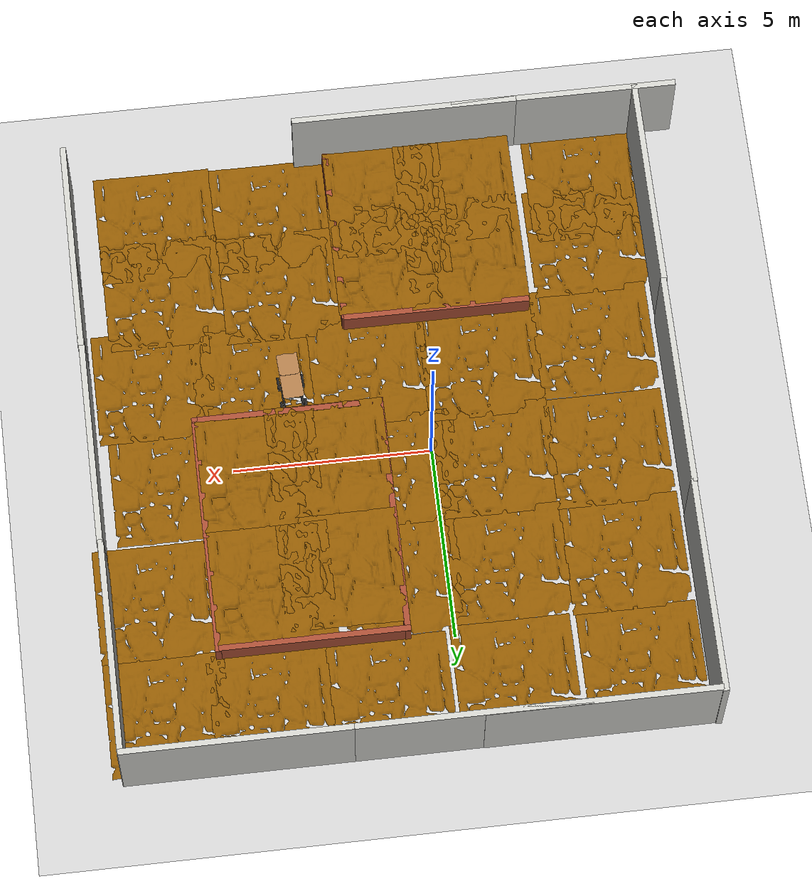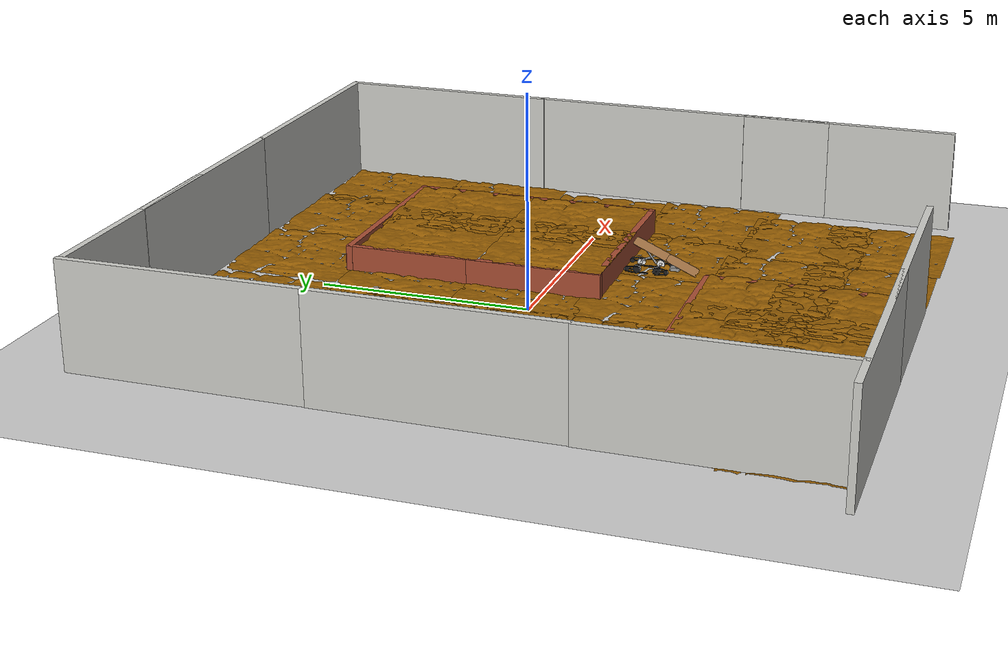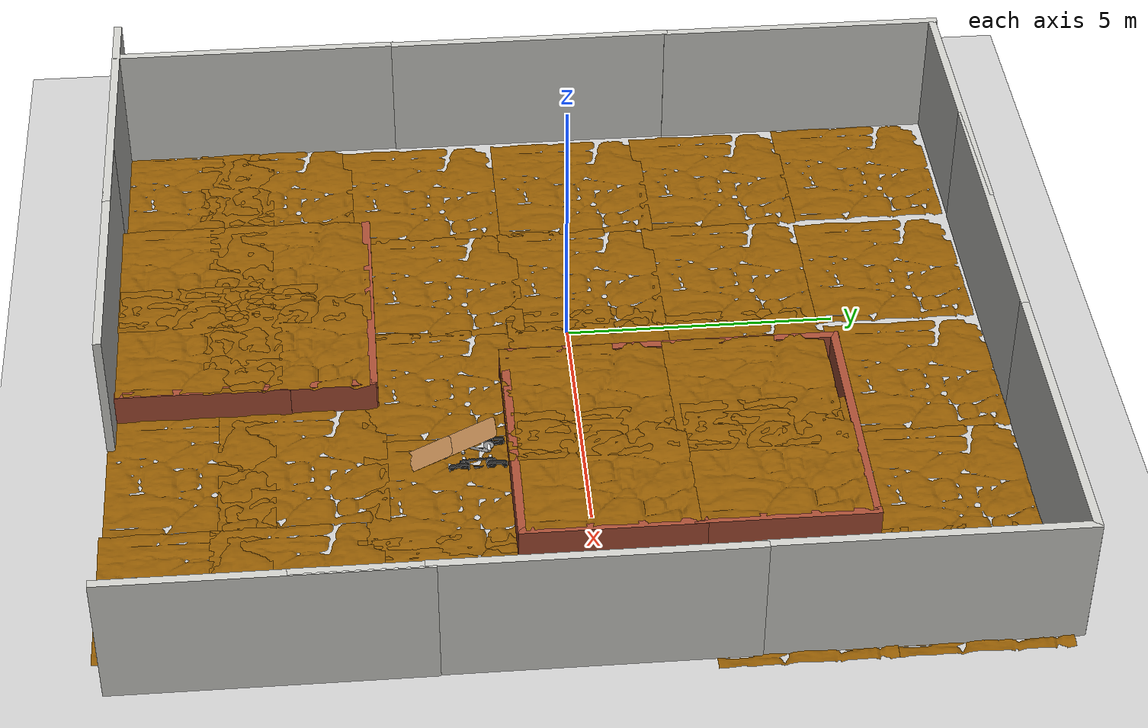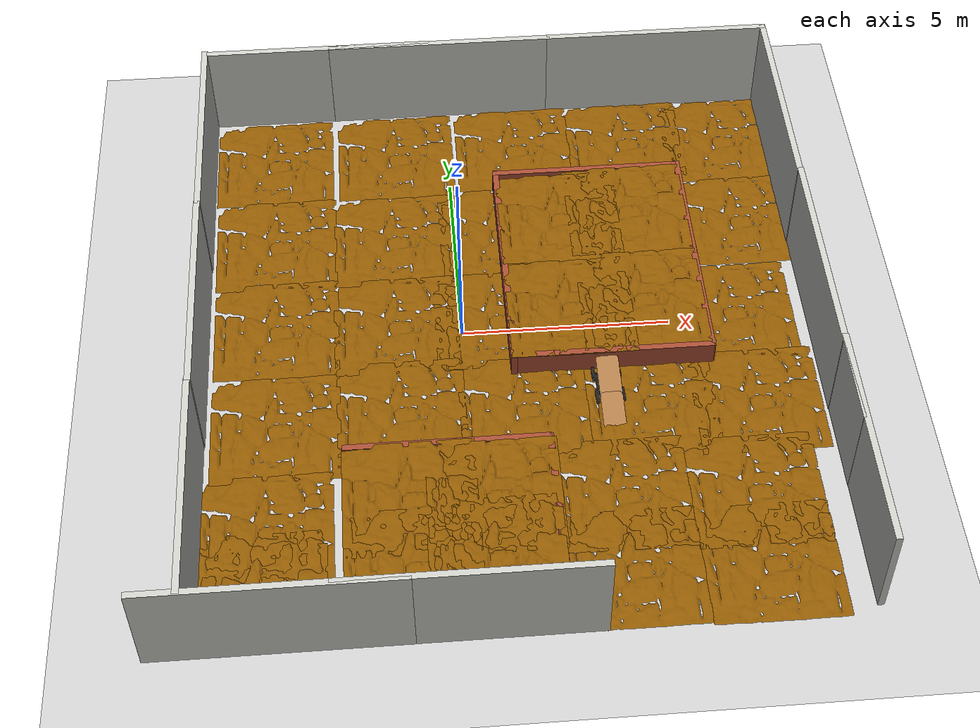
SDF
<sdf version="1.6">
 <world name="default">
  <light name="sun" type="directional">
   <pose>0 0 10 0 -0 0</pose>
   <diffuse>0.8 0.8 0.8 1</diffuse>
   <specular>0.2 0.2 0.2 1</specular>
   <attenuation>
    <range>1000</range>
    <constant>0.9</constant>
    <linear>0.01</linear>
    <quadratic>0.001</quadratic>
   </attenuation>
   <direction>-0.5 0.1 -0.9</direction>
  </light>
  <model name="ground_plane">
   <static>1</static>
   <link name="link">
    <collision name="collision">
     <geometry><plane><normal>0 0 1</normal><size>100 100</size></plane></geometry>
     <surface>
      <contact><collide_bitmask>65535</collide_bitmask></contact>
      <friction><ode><mu>100</mu><mu2>50</mu2></ode></friction>
     </surface>
    </collision>
    <visual name="visual">
     <cast_shadows>0</cast_shadows>
     <geometry><plane><normal>0 0 1</normal><size>100 100</size></plane></geometry>
     <material>
      <script><uri>file://media/materials/scripts/gazebo.material</uri><name>Gazebo/Grey</name></script>
     </material>
    </visual>
   </link>
  </model>
  <gravity>0 0 -9.8</gravity>
  <magnetic_field>6e-06 2.3e-05 -4.2e-05</magnetic_field>
  <atmosphere type="adiabatic"/>
  <physics name="default_physics" default="0" type="ode">
   <max_step_size>0.001</max_step_size>
   <real_time_factor>1</real_time_factor>
   <real_time_update_rate>1000</real_time_update_rate>
  </physics>
  <scene><ambient>0.4 0.4 0.4 1</ambient><background>0.7 0.7 0.7 1</background><shadows>1</shadows></scene>
  <audio><device>default</device></audio>
  <spherical_coordinates>
   <surface_model>EARTH_WGS84</surface_model>
   <latitude_deg>0</latitude_deg>
   <longitude_deg>0</longitude_deg>
   <elevation>0</elevation>
   <heading_deg>0</heading_deg>
  </spherical_coordinates>
  <model name="suelo_alto">
   <link name="link_0">
    <inertial>
     <mass>1</mass>
     <inertia>
      <ixx>0.166667</ixx>
      <ixy>0</ixy>
      <ixz>0</ixz>
      <iyy>0.166667</iyy>
      <iyz>0</iyz>
      <izz>0.166667</izz>
     </inertia>
    </inertial>
    <pose>-2e-06 0 0 0 -0 0</pose>
    <gravity>0</gravity>
    <visual name="visual">
     <pose>0 0 0.6 1.57 -0 0</pose>
     <geometry>
      <mesh>
       <uri>/home/christyan/catkin_sureveg/src/explorador_2/worlds/Plantas/roca2.stl</uri>
       <scale>0.005 0.003 0.005</scale>
      </mesh>
     </geometry>
     <material>
      <lighting>1</lighting>
      <script><uri>file://media/materials/scripts/gazebo.material</uri><name>Gazebo/Grey</name></script>
      <shader type="vertex"><normal_map>__default__</normal_map></shader>
      <ambient>0.561 0.349 0.008 1</ambient>
      <diffuse>0.333 0.341 0.325 1</diffuse>
      <specular>0.561 0.349 0.008 1</specular>
      <emissive>0 0 0 1</emissive>
     </material>
    </visual>
    <collision name="collision">
     <pose>0 0 0.6 1.57 -0 0</pose>
     <geometry>
      <mesh>
       <uri>/home/christyan/catkin_sureveg/src/explorador_2/worlds/Plantas/roca2.stl</uri>
       <scale>0.005 0.003 0.005</scale>
      </mesh>
     </geometry>
     <surface>
      <friction>
       <ode><mu>1</mu><mu2>1</mu2><fdir1>0 0 0</fdir1><slip1>0</slip1><slip2>0</slip2></ode>
       <torsional>
        <coefficient>1</coefficient>
        <patch_radius>0</patch_radius>
        <surface_radius>0</surface_radius>
        <use_patch_radius>1</use_patch_radius>
        <ode><slip>0</slip></ode>
       </torsional>
      </friction>
      <bounce><restitution_coefficient>0</restitution_coefficient><threshold>1e+06</threshold></bounce>
      <contact>
       <collide_without_contact>1</collide_without_contact>
       <collide_without_contact_bitmask>1</collide_without_contact_bitmask>
       <collide_bitmask>1</collide_bitmask>
       <ode>
        <soft_cfm>0</soft_cfm>
        <soft_erp>0.2</soft_erp>
        <kp>1e+13</kp>
        <kd>1</kd>
        <max_vel>0.01</max_vel>
        <min_depth>0</min_depth>
       </ode>
       <bullet>
        <split_impulse>1</split_impulse>
        <split_impulse_penetration_threshold>-0.01</split_impulse_penetration_threshold>
        <soft_cfm>0</soft_cfm>
        <soft_erp>0.2</soft_erp>
        <kp>1e+13</kp>
        <kd>1</kd>
       </bullet>
      </contact>
     </surface>
    </collision>
   </link>
   <static>0</static>
   <pose>2.60693 0.146391 0 0 -0 0</pose>
  </model>
  <model name="pared_corta_ladrillo">
   <pose>1.1558 0.273861 0 0 -0 0</pose>
   <link name="Wall_13">
    <collision name="Wall_13_Collision">
     <geometry><box><size>3.25 0.15 0.6</size></box></geometry>
     <pose>0 0 0.3 0 -0 0</pose>
    </collision>
    <visual name="Wall_13_Visual">
     <pose>0 0 0.3 0 -0 0</pose>
     <geometry><box><size>3.25 0.15 0.6</size></box></geometry>
     <material>
      <script><uri>file://media/materials/scripts/gazebo.material</uri><name>Gazebo/Bricks</name></script>
      <ambient>0.996078 0.47451 0.0196078 1</ambient>
     </material>
     <meta><layer>0</layer></meta>
    </visual>
    <pose>0 -0 0 0 -0 1.5708</pose>
   </link>
   <static>1</static>
  </model>
  <model name="pared_corta_lad_2">
   <pose>3.53067 -1.26114 0 0 -0 0</pose>
   <link name="Wall_19">
    <collision name="Wall_19_Collision">
     <geometry><box><size>4.75 0.15 0.6</size></box></geometry>
     <pose>0 0 0.3 0 -0 0</pose>
    </collision>
    <visual name="Wall_19_Visual">
     <pose>0 0 0.3 0 -0 0</pose>
     <geometry><box><size>4.75 0.15 0.6</size></box></geometry>
     <material>
      <script><uri>file://media/materials/scripts/gazebo.material</uri><name>Gazebo/Bricks</name></script>
      <ambient>1 1 1 1</ambient>
     </material>
     <meta><layer>0</layer></meta>
    </visual>
   </link>
   <static>1</static>
  </model>
  <model name="pared_corta_ladrillo_0">
   <pose>1.15661 3.29537 0 0 -0 0</pose>
   <link name="Wall_13">
    <collision name="Wall_13_Collision">
     <geometry><box><size>3.25 0.15 0.6</size></box></geometry>
     <pose>0 0 0.3 0 -0 0</pose>
    </collision>
    <visual name="Wall_13_Visual">
     <pose>0 0 0.3 0 -0 0</pose>
     <geometry><box><size>3.25 0.15 0.6</size></box></geometry>
     <material>
      <script><uri>file://media/materials/scripts/gazebo.material</uri><name>Gazebo/Bricks</name></script>
      <ambient>0.996078 0.47451 0.0196078 1</ambient>
     </material>
     <meta><layer>0</layer></meta>
    </visual>
    <pose>0 -0 0 0 -0 1.5708</pose>
   </link>
   <static>1</static>
  </model>
  <model name="pared_corta_ladrillo_1">
   <pose>5.85369 0.295655 0 0 -0 0</pose>
   <link name="Wall_13">
    <collision name="Wall_13_Collision">
     <geometry><box><size>3.25 0.15 0.6</size></box></geometry>
     <pose>0 0 0.3 0 -0 0</pose>
    </collision>
    <visual name="Wall_13_Visual">
     <pose>0 0 0.3 0 -0 0</pose>
     <geometry><box><size>3.25 0.15 0.6</size></box></geometry>
     <material>
      <script><uri>file://media/materials/scripts/gazebo.material</uri><name>Gazebo/Bricks</name></script>
      <ambient>0.996078 0.47451 0.0196078 1</ambient>
     </material>
     <meta><layer>0</layer></meta>
    </visual>
    <pose>0 -0 0 0 -0 1.5708</pose>
   </link>
   <static>1</static>
  </model>
  <model name="pared_corta_ladrillo_2">
   <pose>5.84693 3.30125 0 0 -0 0</pose>
   <link name="Wall_13">
    <collision name="Wall_13_Collision">
     <geometry><box><size>3.25 0.15 0.6</size></box></geometry>
     <pose>0 0 0.3 0 -0 0</pose>
    </collision>
    <visual name="Wall_13_Visual">
     <pose>0 0 0.3 0 -0 0</pose>
     <geometry><box><size>3.25 0.15 0.6</size></box></geometry>
     <material>
      <script><uri>file://media/materials/scripts/gazebo.material</uri><name>Gazebo/Bricks</name></script>
      <ambient>0.996078 0.47451 0.0196078 1</ambient>
     </material>
     <meta><layer>0</layer></meta>
    </visual>
    <pose>0 -0 0 0 -0 1.5708</pose>
   </link>
   <static>1</static>
  </model>
  <model name="pared_corta_lad_2_0">
   <pose>3.45558 4.83564 0 0 -0 0</pose>
   <link name="Wall_19">
    <collision name="Wall_19_Collision">
     <geometry><box><size>4.75 0.15 0.6</size></box></geometry>
     <pose>0 0 0.3 0 -0 0</pose>
    </collision>
    <visual name="Wall_19_Visual">
     <pose>0 0 0.3 0 -0 0</pose>
     <geometry><box><size>4.75 0.15 0.6</size></box></geometry>
     <material>
      <script><uri>file://media/materials/scripts/gazebo.material</uri><name>Gazebo/Bricks</name></script>
      <ambient>1 1 1 1</ambient>
     </material>
     <meta><layer>0</layer></meta>
    </visual>
   </link>
   <static>1</static>
  </model>
  <model name="suelo_alto_0">
   <link name="link_0">
    <inertial>
     <mass>1</mass>
     <inertia>
      <ixx>0.166667</ixx>
      <ixy>0</ixy>
      <ixz>0</ixz>
      <iyy>0.166667</iyy>
      <iyz>0</iyz>
      <izz>0.166667</izz>
     </inertia>
    </inertial>
    <pose>-2e-06 0 0 0 -0 0</pose>
    <gravity>0</gravity>
    <visual name="visual">
     <pose>0 0 0.6 1.57 -0 0</pose>
     <geometry>
      <mesh>
       <uri>/home/christyan/catkin_sureveg/src/explorador_2/worlds/Plantas/roca2.stl</uri>
       <scale>0.005 0.003 0.005</scale>
      </mesh>
     </geometry>
     <material>
      <lighting>1</lighting>
      <script><uri>file://media/materials/scripts/gazebo.material</uri><name>Gazebo/Grey</name></script>
      <shader type="vertex"><normal_map>__default__</normal_map></shader>
      <ambient>0.561 0.349 0.008 1</ambient>
      <diffuse>0.333 0.341 0.325 1</diffuse>
      <specular>0.561 0.349 0.008 1</specular>
      <emissive>0 0 0 1</emissive>
     </material>
    </visual>
    <collision name="collision">
     <pose>0 0 0.6 1.57 -0 0</pose>
     <geometry>
      <mesh>
       <uri>/home/christyan/catkin_sureveg/src/explorador_2/worlds/Plantas/roca2.stl</uri>
       <scale>0.005 0.003 0.005</scale>
      </mesh>
     </geometry>
     <surface>
      <friction>
       <ode><mu>1</mu><mu2>1</mu2><fdir1>0 0 0</fdir1><slip1>0</slip1><slip2>0</slip2></ode>
       <torsional>
        <coefficient>1</coefficient>
        <patch_radius>0</patch_radius>
        <surface_radius>0</surface_radius>
        <use_patch_radius>1</use_patch_radius>
        <ode><slip>0</slip></ode>
       </torsional>
      </friction>
      <bounce><restitution_coefficient>0</restitution_coefficient><threshold>1e+06</threshold></bounce>
      <contact>
       <collide_without_contact>1</collide_without_contact>
       <collide_without_contact_bitmask>1</collide_without_contact_bitmask>
       <collide_bitmask>1</collide_bitmask>
       <ode>
        <soft_cfm>0</soft_cfm>
        <soft_erp>0.2</soft_erp>
        <kp>1e+13</kp>
        <kd>1</kd>
        <max_vel>0.01</max_vel>
        <min_depth>0</min_depth>
       </ode>
       <bullet>
        <split_impulse>1</split_impulse>
        <split_impulse_penetration_threshold>-0.01</split_impulse_penetration_threshold>
        <soft_cfm>0</soft_cfm>
        <soft_erp>0.2</soft_erp>
        <kp>1e+13</kp>
        <kd>1</kd>
       </bullet>
      </contact>
     </surface>
    </collision>
   </link>
   <static>0</static>
   <pose>2.62225 3.13264 0 0 -0 0</pose>
  </model>
  <model name="suelo_alto_1">
   <link name="link_0">
    <inertial>
     <mass>1</mass>
     <inertia>
      <ixx>0.166667</ixx>
      <ixy>0</ixy>
      <ixz>0</ixz>
      <iyy>0.166667</iyy>
      <iyz>0</iyz>
      <izz>0.166667</izz>
     </inertia>
    </inertial>
    <pose>-2e-06 0 0 0 -0 0</pose>
    <gravity>0</gravity>
    <visual name="visual">
     <pose>0 0 0.6 1.57 -0 0</pose>
     <geometry>
      <mesh>
       <uri>/home/christyan/catkin_sureveg/src/explorador_2/worlds/Plantas/roca2.stl</uri>
       <scale>0.005 0.003 0.005</scale>
      </mesh>
     </geometry>
     <material>
      <lighting>1</lighting>
      <script><uri>file://media/materials/scripts/gazebo.material</uri><name>Gazebo/Grey</name></script>
      <shader type="vertex"><normal_map>__default__</normal_map></shader>
      <ambient>0.561 0.349 0.008 1</ambient>
      <diffuse>0.333 0.341 0.325 1</diffuse>
      <specular>0.561 0.349 0.008 1</specular>
      <emissive>0 0 0 1</emissive>
     </material>
    </visual>
    <collision name="collision">
     <pose>0 0 0.6 1.57 -0 0</pose>
     <geometry>
      <mesh>
       <uri>/home/christyan/catkin_sureveg/src/explorador_2/worlds/Plantas/roca2.stl</uri>
       <scale>0.005 0.003 0.005</scale>
      </mesh>
     </geometry>
     <surface>
      <friction>
       <ode><mu>1</mu><mu2>1</mu2><fdir1>0 0 0</fdir1><slip1>0</slip1><slip2>0</slip2></ode>
       <torsional>
        <coefficient>1</coefficient>
        <patch_radius>0</patch_radius>
        <surface_radius>0</surface_radius>
        <use_patch_radius>1</use_patch_radius>
        <ode><slip>0</slip></ode>
       </torsional>
      </friction>
      <bounce><restitution_coefficient>0</restitution_coefficient><threshold>1e+06</threshold></bounce>
      <contact>
       <collide_without_contact>1</collide_without_contact>
       <collide_without_contact_bitmask>1</collide_without_contact_bitmask>
       <collide_bitmask>1</collide_bitmask>
       <ode>
        <soft_cfm>0</soft_cfm>
        <soft_erp>0.2</soft_erp>
        <kp>1e+13</kp>
        <kd>1</kd>
        <max_vel>0.01</max_vel>
        <min_depth>0</min_depth>
       </ode>
       <bullet>
        <split_impulse>1</split_impulse>
        <split_impulse_penetration_threshold>-0.01</split_impulse_penetration_threshold>
        <soft_cfm>0</soft_cfm>
        <soft_erp>0.2</soft_erp>
        <kp>1e+13</kp>
        <kd>1</kd>
       </bullet>
      </contact>
     </surface>
    </collision>
   </link>
   <static>0</static>
   <pose>4.36566 0.301741 0 0 -0 0</pose>
  </model>
  <model name="suelo_alto_2">
   <link name="link_0">
    <inertial>
     <mass>1</mass>
     <inertia>
      <ixx>0.166667</ixx>
      <ixy>0</ixy>
      <ixz>0</ixz>
      <iyy>0.166667</iyy>
      <iyz>0</iyz>
      <izz>0.166667</izz>
     </inertia>
    </inertial>
    <pose>-2e-06 0 0 0 -0 0</pose>
    <gravity>0</gravity>
    <visual name="visual">
     <pose>0 0 0.6 1.57 -0 0</pose>
     <geometry>
      <mesh>
       <uri>/home/christyan/catkin_sureveg/src/explorador_2/worlds/Plantas/roca2.stl</uri>
       <scale>0.005 0.003 0.005</scale>
      </mesh>
     </geometry>
     <material>
      <lighting>1</lighting>
      <script><uri>file://media/materials/scripts/gazebo.material</uri><name>Gazebo/Grey</name></script>
      <shader type="vertex"><normal_map>__default__</normal_map></shader>
      <ambient>0.561 0.349 0.008 1</ambient>
      <diffuse>0.333 0.341 0.325 1</diffuse>
      <specular>0.561 0.349 0.008 1</specular>
      <emissive>0 0 0 1</emissive>
     </material>
    </visual>
    <collision name="collision">
     <pose>0 0 0.6 1.57 -0 0</pose>
     <geometry>
      <mesh>
       <uri>/home/christyan/catkin_sureveg/src/explorador_2/worlds/Plantas/roca2.stl</uri>
       <scale>0.005 0.003 0.005</scale>
      </mesh>
     </geometry>
     <surface>
      <friction>
       <ode><mu>1</mu><mu2>1</mu2><fdir1>0 0 0</fdir1><slip1>0</slip1><slip2>0</slip2></ode>
       <torsional>
        <coefficient>1</coefficient>
        <patch_radius>0</patch_radius>
        <surface_radius>0</surface_radius>
        <use_patch_radius>1</use_patch_radius>
        <ode><slip>0</slip></ode>
       </torsional>
      </friction>
      <bounce><restitution_coefficient>0</restitution_coefficient><threshold>1e+06</threshold></bounce>
      <contact>
       <collide_without_contact>1</collide_without_contact>
       <collide_without_contact_bitmask>1</collide_without_contact_bitmask>
       <collide_bitmask>1</collide_bitmask>
       <ode>
        <soft_cfm>0</soft_cfm>
        <soft_erp>0.2</soft_erp>
        <kp>1e+13</kp>
        <kd>1</kd>
        <max_vel>0.01</max_vel>
        <min_depth>0</min_depth>
       </ode>
       <bullet>
        <split_impulse>1</split_impulse>
        <split_impulse_penetration_threshold>-0.01</split_impulse_penetration_threshold>
        <soft_cfm>0</soft_cfm>
        <soft_erp>0.2</soft_erp>
        <kp>1e+13</kp>
        <kd>1</kd>
       </bullet>
      </contact>
     </surface>
    </collision>
   </link>
   <static>0</static>
   <pose>4.34843 3.27788 0 0 -0 0</pose>
  </model>
  <model name="pared_1">
   <pose>-6.14189 5.20533 0 0 -0 0</pose>
   <link name="Wall_21">
    <collision name="Wall_21_Collision">
     <geometry><box><size>5.5 0.15 2.5</size></box></geometry>
     <pose>0 0 1.25 0 -0 0</pose>
    </collision>
    <visual name="Wall_21_Visual">
     <pose>0 0 1.25 0 -0 0</pose>
     <geometry><box><size>5.5 0.15 2.5</size></box></geometry>
     <material>
      <script><uri>file://media/materials/scripts/gazebo.material</uri><name>Gazebo/CeilingTiled</name></script>
      <ambient>1 1 1 1</ambient>
     </material>
     <meta><layer>0</layer></meta>
    </visual>
    <pose>0 0 0 0 -0 -1.5708</pose>
   </link>
   <static>1</static>
  </model>
  <model name="pared_1_0">
   <pose>-6.15747 -0.225974 -0 0 -0 0</pose>
   <link name="Wall_21">
    <collision name="Wall_21_Collision">
     <geometry><box><size>5.5 0.15 2.5</size></box></geometry>
     <pose>0 0 1.25 0 -0 0</pose>
    </collision>
    <visual name="Wall_21_Visual">
     <pose>0 0 1.25 0 -0 0</pose>
     <geometry><box><size>5.5 0.15 2.5</size></box></geometry>
     <material>
      <script><uri>file://media/materials/scripts/gazebo.material</uri><name>Gazebo/CeilingTiled</name></script>
      <ambient>1 1 1 1</ambient>
     </material>
     <meta><layer>0</layer></meta>
    </visual>
    <pose>0 0 0 0 -0 -1.5708</pose>
   </link>
   <static>1</static>
  </model>
  <model name="pared_1_1">
   <pose>-6.17787 -5.68421 0 0 -0 0</pose>
   <link name="Wall_21">
    <collision name="Wall_21_Collision">
     <geometry><box><size>5.5 0.15 2.5</size></box></geometry>
     <pose>0 0 1.25 0 -0 0</pose>
    </collision>
    <visual name="Wall_21_Visual">
     <pose>0 0 1.25 0 -0 0</pose>
     <geometry><box><size>5.5 0.15 2.5</size></box></geometry>
     <material>
      <script><uri>file://media/materials/scripts/gazebo.material</uri><name>Gazebo/CeilingTiled</name></script>
      <ambient>1 1 1 1</ambient>
     </material>
     <meta><layer>0</layer></meta>
    </visual>
    <pose>0 0 0 0 -0 -1.5708</pose>
   </link>
   <static>1</static>
  </model>
  <model name="pared_2">
   <pose>-0.074522 7.8419 0 0 -0 0</pose>
   <link name="Wall_24">
    <collision name="Wall_24_Collision">
     <geometry><box><size>5.75 0.15 2.5</size></box></geometry>
     <pose>0 0 1.25 0 -0 0</pose>
    </collision>
    <visual name="Wall_24_Visual">
     <pose>0 0 1.25 0 -0 0</pose>
     <geometry><box><size>5.75 0.15 2.5</size></box></geometry>
     <material>
      <script><uri>file://media/materials/scripts/gazebo.material</uri><name>Gazebo/CeilingTiled</name></script>
      <ambient>1 1 1 1</ambient>
     </material>
     <meta><layer>0</layer></meta>
    </visual>
   </link>
   <static>1</static>
  </model>
  <model name="pared_2_0">
   <pose>5.59936 7.8412 0 0 -0 0</pose>
   <link name="Wall_24">
    <collision name="Wall_24_Collision">
     <geometry><box><size>5.75 0.15 2.5</size></box></geometry>
     <pose>0 0 1.25 0 -0 0</pose>
    </collision>
    <visual name="Wall_24_Visual">
     <pose>0 0 1.25 0 -0 0</pose>
     <geometry><box><size>5.75 0.15 2.5</size></box></geometry>
     <material>
      <script><uri>file://media/materials/scripts/gazebo.material</uri><name>Gazebo/CeilingTiled</name></script>
      <ambient>1 1 1 1</ambient>
     </material>
     <meta><layer>0</layer></meta>
    </visual>
   </link>
   <static>1</static>
  </model>
  <model name="pared_1_2">
   <pose>8.41269 5.15772 0 0 -0 0</pose>
   <link name="Wall_21">
    <collision name="Wall_21_Collision">
     <geometry><box><size>5.5 0.15 2.5</size></box></geometry>
     <pose>0 0 1.25 0 -0 0</pose>
    </collision>
    <visual name="Wall_21_Visual">
     <pose>0 0 1.25 0 -0 0</pose>
     <geometry><box><size>5.5 0.15 2.5</size></box></geometry>
     <material>
      <script><uri>file://media/materials/scripts/gazebo.material</uri><name>Gazebo/CeilingTiled</name></script>
      <ambient>1 1 1 1</ambient>
     </material>
     <meta><layer>0</layer></meta>
    </visual>
    <pose>0 0 0 0 -0 -1.5708</pose>
   </link>
   <static>1</static>
  </model>
  <model name="pared_1_3">
   <pose>8.43088 -0.22917 0 0 -0 0</pose>
   <link name="Wall_21">
    <collision name="Wall_21_Collision">
     <geometry><box><size>5.5 0.15 2.5</size></box></geometry>
     <pose>0 0 1.25 0 -0 0</pose>
    </collision>
    <visual name="Wall_21_Visual">
     <pose>0 0 1.25 0 -0 0</pose>
     <geometry><box><size>5.5 0.15 2.5</size></box></geometry>
     <material>
      <script><uri>file://media/materials/scripts/gazebo.material</uri><name>Gazebo/CeilingTiled</name></script>
      <ambient>1 1 1 1</ambient>
     </material>
     <meta><layer>0</layer></meta>
    </visual>
    <pose>0 0 0 0 -0 -1.5708</pose>
   </link>
   <static>1</static>
  </model>
  <model name="pared4">
   <pose>8.44328 -4.0336 0 0 -0 0</pose>
   <link name="Wall_28">
    <collision name="Wall_28_Collision">
     <geometry><box><size>2.25 0.15 2.5</size></box></geometry>
     <pose>0 0 1.25 0 -0 0</pose>
    </collision>
    <visual name="Wall_28_Visual">
     <pose>0 0 1.25 0 -0 0</pose>
     <geometry><box><size>2.25 0.15 2.5</size></box></geometry>
     <material>
      <script><uri>file://media/materials/scripts/gazebo.material</uri><name>Gazebo/CeilingTiled</name></script>
      <ambient>1 1 1 1</ambient>
     </material>
     <meta><layer>0</layer></meta>
    </visual>
    <pose>-0 0 0 0 -0 -1.5708</pose>
   </link>
   <static>1</static>
  </model>
  <model name="pared_2_2">
   <pose>-0.261836 -8.38493 0 0 -0 0</pose>
   <link name="Wall_24">
    <collision name="Wall_24_Collision">
     <geometry><box><size>5.75 0.15 2.5</size></box></geometry>
     <pose>0 0 1.25 0 -0 0</pose>
    </collision>
    <visual name="Wall_24_Visual">
     <pose>0 0 1.25 0 -0 0</pose>
     <geometry><box><size>5.75 0.15 2.5</size></box></geometry>
     <material>
      <script><uri>file://media/materials/scripts/gazebo.material</uri><name>Gazebo/CeilingTiled</name></script>
      <ambient>1 1 1 1</ambient>
     </material>
     <meta><layer>0</layer></meta>
    </visual>
   </link>
   <static>1</static>
  </model>
  <model name="pared_1_4">
   <pose>8.44952 -5.53816 0 0 -0 0</pose>
   <link name="Wall_21">
    <collision name="Wall_21_Collision">
     <geometry><box><size>5.5 0.15 2.5</size></box></geometry>
     <pose>0 0 1.25 0 -0 0</pose>
    </collision>
    <visual name="Wall_21_Visual">
     <pose>0 0 1.25 0 -0 0</pose>
     <geometry><box><size>5.5 0.15 2.5</size></box></geometry>
     <material>
      <script><uri>file://media/materials/scripts/gazebo.material</uri><name>Gazebo/CeilingTiled</name></script>
      <ambient>1 1 1 1</ambient>
     </material>
     <meta><layer>0</layer></meta>
    </visual>
    <pose>0 0 0 0 -0 -1.5708</pose>
   </link>
   <static>1</static>
  </model>
  <model name="suelo_1_1">
   <link name="link_0">
    <inertial>
     <mass>1</mass>
     <inertia>
      <ixx>0.166667</ixx>
      <ixy>0</ixy>
      <ixz>0</ixz>
      <iyy>0.166667</iyy>
      <iyz>0</iyz>
      <izz>0.166667</izz>
     </inertia>
    </inertial>
    <pose>-2e-06 0 0 0 -0 0</pose>
    <gravity>0</gravity>
    <visual name="visual">
     <pose>0 0 0 1.57 -0 0</pose>
     <geometry>
      <mesh>
       <uri>/home/christyan/catkin_sureveg/src/explorador_2/worlds/Plantas/roca2.stl</uri>
       <scale>0.005 0.003 0.005</scale>
      </mesh>
     </geometry>
     <material>
      <lighting>1</lighting>
      <script><uri>file://media/materials/scripts/gazebo.material</uri><name>Gazebo/Grey</name></script>
      <shader type="vertex"><normal_map>__default__</normal_map></shader>
      <ambient>0.561 0.349 0.008 1</ambient>
      <diffuse>0.333 0.341 0.325 1</diffuse>
      <specular>0.561 0.349 0.008 1</specular>
      <emissive>0 0 0 1</emissive>
     </material>
    </visual>
    <collision name="collision">
     <pose>0 0 0 1.57 -0 0</pose>
     <geometry>
      <mesh>
       <uri>/home/christyan/catkin_sureveg/src/explorador_2/worlds/Plantas/roca2.stl</uri>
       <scale>0.005 0.003 0.005</scale>
      </mesh>
     </geometry>
     <surface>
      <friction>
       <ode><mu>1</mu><mu2>1</mu2><fdir1>0 0 0</fdir1><slip1>0</slip1><slip2>0</slip2></ode>
       <torsional>
        <coefficient>1</coefficient>
        <patch_radius>0</patch_radius>
        <surface_radius>0</surface_radius>
        <use_patch_radius>1</use_patch_radius>
        <ode><slip>0</slip></ode>
       </torsional>
      </friction>
      <bounce><restitution_coefficient>0</restitution_coefficient><threshold>1e+06</threshold></bounce>
      <contact>
       <collide_without_contact>1</collide_without_contact>
       <collide_without_contact_bitmask>1</collide_without_contact_bitmask>
       <collide_bitmask>1</collide_bitmask>
       <ode>
        <soft_cfm>0</soft_cfm>
        <soft_erp>0.2</soft_erp>
        <kp>1e+13</kp>
        <kd>1</kd>
        <max_vel>0.01</max_vel>
        <min_depth>0</min_depth>
       </ode>
       <bullet>
        <split_impulse>1</split_impulse>
        <split_impulse_penetration_threshold>-0.01</split_impulse_penetration_threshold>
        <soft_cfm>0</soft_cfm>
        <soft_erp>0.2</soft_erp>
        <kp>1e+13</kp>
        <kd>1</kd>
       </bullet>
      </contact>
     </surface>
    </collision>
   </link>
   <static>0</static>
   <pose>1.72058 6.30894 0 0 -0 0</pose>
  </model>
  <model name="suelo_1">
   <link name="link_0">
    <inertial>
     <mass>1</mass>
     <inertia>
      <ixx>0.166667</ixx>
      <ixy>0</ixy>
      <ixz>0</ixz>
      <iyy>0.166667</iyy>
      <iyz>0</iyz>
      <izz>0.166667</izz>
     </inertia>
    </inertial>
    <pose>-2e-06 0 0 0 -0 0</pose>
    <gravity>0</gravity>
    <visual name="visual">
     <pose>0 0 0 1.57 -0 0</pose>
     <geometry>
      <mesh>
       <uri>/home/christyan/catkin_sureveg/src/explorador_2/worlds/Plantas/roca2.stl</uri>
       <scale>0.005 0.003 0.005</scale>
      </mesh>
     </geometry>
     <material>
      <lighting>1</lighting>
      <script><uri>file://media/materials/scripts/gazebo.material</uri><name>Gazebo/Grey</name></script>
      <shader type="vertex"><normal_map>__default__</normal_map></shader>
      <ambient>0.561 0.349 0.008 1</ambient>
      <diffuse>0.333 0.341 0.325 1</diffuse>
      <specular>0.561 0.349 0.008 1</specular>
      <emissive>0 0 0 1</emissive>
     </material>
    </visual>
    <collision name="collision">
     <pose>0 0 0 1.57 -0 0</pose>
     <geometry>
      <mesh>
       <uri>/home/christyan/catkin_sureveg/src/explorador_2/worlds/Plantas/roca2.stl</uri>
       <scale>0.005 0.003 0.005</scale>
      </mesh>
     </geometry>
     <surface>
      <friction>
       <ode><mu>1</mu><mu2>1</mu2><fdir1>0 0 0</fdir1><slip1>0</slip1><slip2>0</slip2></ode>
       <torsional>
        <coefficient>1</coefficient>
        <patch_radius>0</patch_radius>
        <surface_radius>0</surface_radius>
        <use_patch_radius>1</use_patch_radius>
        <ode><slip>0</slip></ode>
       </torsional>
      </friction>
      <bounce><restitution_coefficient>0</restitution_coefficient><threshold>1e+06</threshold></bounce>
      <contact>
       <collide_without_contact>1</collide_without_contact>
       <collide_without_contact_bitmask>1</collide_without_contact_bitmask>
       <collide_bitmask>1</collide_bitmask>
       <ode>
        <soft_cfm>0</soft_cfm>
        <soft_erp>0.2</soft_erp>
        <kp>1e+13</kp>
        <kd>1</kd>
        <max_vel>0.01</max_vel>
        <min_depth>0</min_depth>
       </ode>
       <bullet>
        <split_impulse>1</split_impulse>
        <split_impulse_penetration_threshold>-0.01</split_impulse_penetration_threshold>
        <soft_cfm>0</soft_cfm>
        <soft_erp>0.2</soft_erp>
        <kp>1e+13</kp>
        <kd>1</kd>
       </bullet>
      </contact>
     </surface>
    </collision>
   </link>
   <static>0</static>
   <pose>-1.38068 6.20388 0 0 -0 0</pose>
  </model>
  <model name="suelo_1_0">
   <link name="link_0">
    <inertial>
     <mass>1</mass>
     <inertia>
      <ixx>0.166667</ixx>
      <ixy>0</ixy>
      <ixz>0</ixz>
      <iyy>0.166667</iyy>
      <iyz>0</iyz>
      <izz>0.166667</izz>
     </inertia>
    </inertial>
    <pose>-2e-06 0 0 0 -0 0</pose>
    <gravity>0</gravity>
    <visual name="visual">
     <pose>0 0 0 1.57 -0 0</pose>
     <geometry>
      <mesh>
       <uri>/home/christyan/catkin_sureveg/src/explorador_2/worlds/Plantas/roca2.stl</uri>
       <scale>0.005 0.003 0.005</scale>
      </mesh>
     </geometry>
     <material>
      <lighting>1</lighting>
      <script><uri>file://media/materials/scripts/gazebo.material</uri><name>Gazebo/Grey</name></script>
      <shader type="vertex"><normal_map>__default__</normal_map></shader>
      <ambient>0.561 0.349 0.008 1</ambient>
      <diffuse>0.333 0.341 0.325 1</diffuse>
      <specular>0.561 0.349 0.008 1</specular>
      <emissive>0 0 0 1</emissive>
     </material>
    </visual>
    <collision name="collision">
     <pose>0 0 0 1.57 -0 0</pose>
     <geometry>
      <mesh>
       <uri>/home/christyan/catkin_sureveg/src/explorador_2/worlds/Plantas/roca2.stl</uri>
       <scale>0.005 0.003 0.005</scale>
      </mesh>
     </geometry>
     <surface>
      <friction>
       <ode><mu>1</mu><mu2>1</mu2><fdir1>0 0 0</fdir1><slip1>0</slip1><slip2>0</slip2></ode>
       <torsional>
        <coefficient>1</coefficient>
        <patch_radius>0</patch_radius>
        <surface_radius>0</surface_radius>
        <use_patch_radius>1</use_patch_radius>
        <ode><slip>0</slip></ode>
       </torsional>
      </friction>
      <bounce><restitution_coefficient>0</restitution_coefficient><threshold>1e+06</threshold></bounce>
      <contact>
       <collide_without_contact>1</collide_without_contact>
       <collide_without_contact_bitmask>1</collide_without_contact_bitmask>
       <collide_bitmask>1</collide_bitmask>
       <ode>
        <soft_cfm>0</soft_cfm>
        <soft_erp>0.2</soft_erp>
        <kp>1e+13</kp>
        <kd>1</kd>
        <max_vel>0.01</max_vel>
        <min_depth>0</min_depth>
       </ode>
       <bullet>
        <split_impulse>1</split_impulse>
        <split_impulse_penetration_threshold>-0.01</split_impulse_penetration_threshold>
        <soft_cfm>0</soft_cfm>
        <soft_erp>0.2</soft_erp>
        <kp>1e+13</kp>
        <kd>1</kd>
       </bullet>
      </contact>
     </surface>
    </collision>
   </link>
   <static>0</static>
   <pose>-1.5235 3.21161 0 0 -0 0</pose>
  </model>
  <model name="suelo_1_2">
   <link name="link_0">
    <inertial>
     <mass>1</mass>
     <inertia>
      <ixx>0.166667</ixx>
      <ixy>0</ixy>
      <ixz>0</ixz>
      <iyy>0.166667</iyy>
      <iyz>0</iyz>
      <izz>0.166667</izz>
     </inertia>
    </inertial>
    <pose>-2e-06 0 0 0 -0 0</pose>
    <gravity>0</gravity>
    <visual name="visual">
     <pose>0 0 0 1.57 -0 0</pose>
     <geometry>
      <mesh>
       <uri>/home/christyan/catkin_sureveg/src/explorador_2/worlds/Plantas/roca2.stl</uri>
       <scale>0.005 0.003 0.005</scale>
      </mesh>
     </geometry>
     <material>
      <lighting>1</lighting>
      <script><uri>file://media/materials/scripts/gazebo.material</uri><name>Gazebo/Grey</name></script>
      <shader type="vertex"><normal_map>__default__</normal_map></shader>
      <ambient>0.561 0.349 0.008 1</ambient>
      <diffuse>0.333 0.341 0.325 1</diffuse>
      <specular>0.561 0.349 0.008 1</specular>
      <emissive>0 0 0 1</emissive>
     </material>
    </visual>
    <collision name="collision">
     <pose>0 0 0 1.57 -0 0</pose>
     <geometry>
      <mesh>
       <uri>/home/christyan/catkin_sureveg/src/explorador_2/worlds/Plantas/roca2.stl</uri>
       <scale>0.005 0.003 0.005</scale>
      </mesh>
     </geometry>
     <surface>
      <friction>
       <ode><mu>1</mu><mu2>1</mu2><fdir1>0 0 0</fdir1><slip1>0</slip1><slip2>0</slip2></ode>
       <torsional>
        <coefficient>1</coefficient>
        <patch_radius>0</patch_radius>
        <surface_radius>0</surface_radius>
        <use_patch_radius>1</use_patch_radius>
        <ode><slip>0</slip></ode>
       </torsional>
      </friction>
      <bounce><restitution_coefficient>0</restitution_coefficient><threshold>1e+06</threshold></bounce>
      <contact>
       <collide_without_contact>1</collide_without_contact>
       <collide_without_contact_bitmask>1</collide_without_contact_bitmask>
       <collide_bitmask>1</collide_bitmask>
       <ode>
        <soft_cfm>0</soft_cfm>
        <soft_erp>0.2</soft_erp>
        <kp>1e+13</kp>
        <kd>1</kd>
        <max_vel>0.01</max_vel>
        <min_depth>0</min_depth>
       </ode>
       <bullet>
        <split_impulse>1</split_impulse>
        <split_impulse_penetration_threshold>-0.01</split_impulse_penetration_threshold>
        <soft_cfm>0</soft_cfm>
        <soft_erp>0.2</soft_erp>
        <kp>1e+13</kp>
        <kd>1</kd>
       </bullet>
      </contact>
     </surface>
    </collision>
   </link>
   <static>0</static>
   <pose>1.12817 3.30368 0 0 -0 0</pose>
  </model>
  <model name="suelo_1_3">
   <link name="link_0">
    <inertial>
     <mass>1</mass>
     <inertia>
      <ixx>0.166667</ixx>
      <ixy>0</ixy>
      <ixz>0</ixz>
      <iyy>0.166667</iyy>
      <iyz>0</iyz>
      <izz>0.166667</izz>
     </inertia>
    </inertial>
    <pose>-2e-06 0 0 0 -0 0</pose>
    <gravity>0</gravity>
    <visual name="visual">
     <pose>0 0 0 1.57 -0 0</pose>
     <geometry>
      <mesh>
       <uri>/home/christyan/catkin_sureveg/src/explorador_2/worlds/Plantas/roca2.stl</uri>
       <scale>0.005 0.003 0.005</scale>
      </mesh>
     </geometry>
     <material>
      <lighting>1</lighting>
      <script><uri>file://media/materials/scripts/gazebo.material</uri><name>Gazebo/Grey</name></script>
      <shader type="vertex"><normal_map>__default__</normal_map></shader>
      <ambient>0.561 0.349 0.008 1</ambient>
      <diffuse>0.333 0.341 0.325 1</diffuse>
      <specular>0.561 0.349 0.008 1</specular>
      <emissive>0 0 0 1</emissive>
     </material>
    </visual>
    <collision name="collision">
     <pose>0 0 0 1.57 -0 0</pose>
     <geometry>
      <mesh>
       <uri>/home/christyan/catkin_sureveg/src/explorador_2/worlds/Plantas/roca2.stl</uri>
       <scale>0.005 0.003 0.005</scale>
      </mesh>
     </geometry>
     <surface>
      <friction>
       <ode><mu>1</mu><mu2>1</mu2><fdir1>0 0 0</fdir1><slip1>0</slip1><slip2>0</slip2></ode>
       <torsional>
        <coefficient>1</coefficient>
        <patch_radius>0</patch_radius>
        <surface_radius>0</surface_radius>
        <use_patch_radius>1</use_patch_radius>
        <ode><slip>0</slip></ode>
       </torsional>
      </friction>
      <bounce><restitution_coefficient>0</restitution_coefficient><threshold>1e+06</threshold></bounce>
      <contact>
       <collide_without_contact>1</collide_without_contact>
       <collide_without_contact_bitmask>1</collide_without_contact_bitmask>
       <collide_bitmask>1</collide_bitmask>
       <ode>
        <soft_cfm>0</soft_cfm>
        <soft_erp>0.2</soft_erp>
        <kp>1e+13</kp>
        <kd>1</kd>
        <max_vel>0.01</max_vel>
        <min_depth>0</min_depth>
       </ode>
       <bullet>
        <split_impulse>1</split_impulse>
        <split_impulse_penetration_threshold>-0.01</split_impulse_penetration_threshold>
        <soft_cfm>0</soft_cfm>
        <soft_erp>0.2</soft_erp>
        <kp>1e+13</kp>
        <kd>1</kd>
       </bullet>
      </contact>
     </surface>
    </collision>
   </link>
   <static>0</static>
   <pose>-1.57932 0.383769 0 0 -0 0</pose>
  </model>
  <model name="suelo_1_4">
   <link name="link_0">
    <inertial>
     <mass>1</mass>
     <inertia>
      <ixx>0.166667</ixx>
      <ixy>0</ixy>
      <ixz>0</ixz>
      <iyy>0.166667</iyy>
      <iyz>0</iyz>
      <izz>0.166667</izz>
     </inertia>
    </inertial>
    <pose>-2e-06 0 0 0 -0 0</pose>
    <gravity>0</gravity>
    <visual name="visual">
     <pose>0 0 0 1.57 -0 0</pose>
     <geometry>
      <mesh>
       <uri>/home/christyan/catkin_sureveg/src/explorador_2/worlds/Plantas/roca2.stl</uri>
       <scale>0.005 0.003 0.005</scale>
      </mesh>
     </geometry>
     <material>
      <lighting>1</lighting>
      <script><uri>file://media/materials/scripts/gazebo.material</uri><name>Gazebo/Grey</name></script>
      <shader type="vertex"><normal_map>__default__</normal_map></shader>
      <ambient>0.561 0.349 0.008 1</ambient>
      <diffuse>0.333 0.341 0.325 1</diffuse>
      <specular>0.561 0.349 0.008 1</specular>
      <emissive>0 0 0 1</emissive>
     </material>
    </visual>
    <collision name="collision">
     <pose>0 0 0 1.57 -0 0</pose>
     <geometry>
      <mesh>
       <uri>/home/christyan/catkin_sureveg/src/explorador_2/worlds/Plantas/roca2.stl</uri>
       <scale>0.005 0.003 0.005</scale>
      </mesh>
     </geometry>
     <surface>
      <friction>
       <ode><mu>1</mu><mu2>1</mu2><fdir1>0 0 0</fdir1><slip1>0</slip1><slip2>0</slip2></ode>
       <torsional>
        <coefficient>1</coefficient>
        <patch_radius>0</patch_radius>
        <surface_radius>0</surface_radius>
        <use_patch_radius>1</use_patch_radius>
        <ode><slip>0</slip></ode>
       </torsional>
      </friction>
      <bounce><restitution_coefficient>0</restitution_coefficient><threshold>1e+06</threshold></bounce>
      <contact>
       <collide_without_contact>1</collide_without_contact>
       <collide_without_contact_bitmask>1</collide_without_contact_bitmask>
       <collide_bitmask>1</collide_bitmask>
       <ode>
        <soft_cfm>0</soft_cfm>
        <soft_erp>0.2</soft_erp>
        <kp>1e+13</kp>
        <kd>1</kd>
        <max_vel>0.01</max_vel>
        <min_depth>0</min_depth>
       </ode>
       <bullet>
        <split_impulse>1</split_impulse>
        <split_impulse_penetration_threshold>-0.01</split_impulse_penetration_threshold>
        <soft_cfm>0</soft_cfm>
        <soft_erp>0.2</soft_erp>
        <kp>1e+13</kp>
        <kd>1</kd>
       </bullet>
      </contact>
     </surface>
    </collision>
   </link>
   <static>0</static>
   <pose>0.861675 0.391435 0 0 -0 0</pose>
  </model>
  <model name="suelo_1_5">
   <link name="link_0">
    <inertial>
     <mass>1</mass>
     <inertia>
      <ixx>0.166667</ixx>
      <ixy>0</ixy>
      <ixz>0</ixz>
      <iyy>0.166667</iyy>
      <iyz>0</iyz>
      <izz>0.166667</izz>
     </inertia>
    </inertial>
    <pose>-2e-06 0 0 0 -0 0</pose>
    <gravity>0</gravity>
    <visual name="visual">
     <pose>0 0 0 1.57 -0 0</pose>
     <geometry>
      <mesh>
       <uri>/home/christyan/catkin_sureveg/src/explorador_2/worlds/Plantas/roca2.stl</uri>
       <scale>0.005 0.003 0.005</scale>
      </mesh>
     </geometry>
     <material>
      <lighting>1</lighting>
      <script><uri>file://media/materials/scripts/gazebo.material</uri><name>Gazebo/Grey</name></script>
      <shader type="vertex"><normal_map>__default__</normal_map></shader>
      <ambient>0.561 0.349 0.008 1</ambient>
      <diffuse>0.333 0.341 0.325 1</diffuse>
      <specular>0.561 0.349 0.008 1</specular>
      <emissive>0 0 0 1</emissive>
     </material>
    </visual>
    <collision name="collision">
     <pose>0 0 0 1.57 -0 0</pose>
     <geometry>
      <mesh>
       <uri>/home/christyan/catkin_sureveg/src/explorador_2/worlds/Plantas/roca2.stl</uri>
       <scale>0.005 0.003 0.005</scale>
      </mesh>
     </geometry>
     <surface>
      <friction>
       <ode><mu>1</mu><mu2>1</mu2><fdir1>0 0 0</fdir1><slip1>0</slip1><slip2>0</slip2></ode>
       <torsional>
        <coefficient>1</coefficient>
        <patch_radius>0</patch_radius>
        <surface_radius>0</surface_radius>
        <use_patch_radius>1</use_patch_radius>
        <ode><slip>0</slip></ode>
       </torsional>
      </friction>
      <bounce><restitution_coefficient>0</restitution_coefficient><threshold>1e+06</threshold></bounce>
      <contact>
       <collide_without_contact>1</collide_without_contact>
       <collide_without_contact_bitmask>1</collide_without_contact_bitmask>
       <collide_bitmask>1</collide_bitmask>
       <ode>
        <soft_cfm>0</soft_cfm>
        <soft_erp>0.2</soft_erp>
        <kp>1e+13</kp>
        <kd>1</kd>
        <max_vel>0.01</max_vel>
        <min_depth>0</min_depth>
       </ode>
       <bullet>
        <split_impulse>1</split_impulse>
        <split_impulse_penetration_threshold>-0.01</split_impulse_penetration_threshold>
        <soft_cfm>0</soft_cfm>
        <soft_erp>0.2</soft_erp>
        <kp>1e+13</kp>
        <kd>1</kd>
       </bullet>
      </contact>
     </surface>
    </collision>
   </link>
   <static>0</static>
   <pose>4.68724 6.33488 0 0 -0 0</pose>
  </model>
  <model name="suelo_1_6">
   <link name="link_0">
    <inertial>
     <mass>1</mass>
     <inertia>
      <ixx>0.166667</ixx>
      <ixy>0</ixy>
      <ixz>0</ixz>
      <iyy>0.166667</iyy>
      <iyz>0</iyz>
      <izz>0.166667</izz>
     </inertia>
    </inertial>
    <pose>-2e-06 0 0 0 -0 0</pose>
    <gravity>0</gravity>
    <visual name="visual">
     <pose>0 0 0 1.57 -0 0</pose>
     <geometry>
      <mesh>
       <uri>/home/christyan/catkin_sureveg/src/explorador_2/worlds/Plantas/roca2.stl</uri>
       <scale>0.005 0.003 0.005</scale>
      </mesh>
     </geometry>
     <material>
      <lighting>1</lighting>
      <script><uri>file://media/materials/scripts/gazebo.material</uri><name>Gazebo/Grey</name></script>
      <shader type="vertex"><normal_map>__default__</normal_map></shader>
      <ambient>0.561 0.349 0.008 1</ambient>
      <diffuse>0.333 0.341 0.325 1</diffuse>
      <specular>0.561 0.349 0.008 1</specular>
      <emissive>0 0 0 1</emissive>
     </material>
    </visual>
    <collision name="collision">
     <pose>0 0 0 1.57 -0 0</pose>
     <geometry>
      <mesh>
       <uri>/home/christyan/catkin_sureveg/src/explorador_2/worlds/Plantas/roca2.stl</uri>
       <scale>0.005 0.003 0.005</scale>
      </mesh>
     </geometry>
     <surface>
      <friction>
       <ode><mu>1</mu><mu2>1</mu2><fdir1>0 0 0</fdir1><slip1>0</slip1><slip2>0</slip2></ode>
       <torsional>
        <coefficient>1</coefficient>
        <patch_radius>0</patch_radius>
        <surface_radius>0</surface_radius>
        <use_patch_radius>1</use_patch_radius>
        <ode><slip>0</slip></ode>
       </torsional>
      </friction>
      <bounce><restitution_coefficient>0</restitution_coefficient><threshold>1e+06</threshold></bounce>
      <contact>
       <collide_without_contact>1</collide_without_contact>
       <collide_without_contact_bitmask>1</collide_without_contact_bitmask>
       <collide_bitmask>1</collide_bitmask>
       <ode>
        <soft_cfm>0</soft_cfm>
        <soft_erp>0.2</soft_erp>
        <kp>1e+13</kp>
        <kd>1</kd>
        <max_vel>0.01</max_vel>
        <min_depth>0</min_depth>
       </ode>
       <bullet>
        <split_impulse>1</split_impulse>
        <split_impulse_penetration_threshold>-0.01</split_impulse_penetration_threshold>
        <soft_cfm>0</soft_cfm>
        <soft_erp>0.2</soft_erp>
        <kp>1e+13</kp>
        <kd>1</kd>
       </bullet>
      </contact>
     </surface>
    </collision>
   </link>
   <static>0</static>
   <pose>7.22593 6.2212 0 0 -0 0</pose>
  </model>
  <model name="suelo_1_7">
   <link name="link_0">
    <inertial>
     <mass>1</mass>
     <inertia>
      <ixx>0.166667</ixx>
      <ixy>0</ixy>
      <ixz>0</ixz>
      <iyy>0.166667</iyy>
      <iyz>0</iyz>
      <izz>0.166667</izz>
     </inertia>
    </inertial>
    <pose>-2e-06 0 0 0 -0 0</pose>
    <gravity>0</gravity>
    <visual name="visual">
     <pose>0 0 0 1.57 -0 0</pose>
     <geometry>
      <mesh>
       <uri>/home/christyan/catkin_sureveg/src/explorador_2/worlds/Plantas/roca2.stl</uri>
       <scale>0.005 0.003 0.005</scale>
      </mesh>
     </geometry>
     <material>
      <lighting>1</lighting>
      <script><uri>file://media/materials/scripts/gazebo.material</uri><name>Gazebo/Grey</name></script>
      <shader type="vertex"><normal_map>__default__</normal_map></shader>
      <ambient>0.561 0.349 0.008 1</ambient>
      <diffuse>0.333 0.341 0.325 1</diffuse>
      <specular>0.561 0.349 0.008 1</specular>
      <emissive>0 0 0 1</emissive>
     </material>
    </visual>
    <collision name="collision">
     <pose>0 0 0 1.57 -0 0</pose>
     <geometry>
      <mesh>
       <uri>/home/christyan/catkin_sureveg/src/explorador_2/worlds/Plantas/roca2.stl</uri>
       <scale>0.005 0.003 0.005</scale>
      </mesh>
     </geometry>
     <surface>
      <friction>
       <ode><mu>1</mu><mu2>1</mu2><fdir1>0 0 0</fdir1><slip1>0</slip1><slip2>0</slip2></ode>
       <torsional>
        <coefficient>1</coefficient>
        <patch_radius>0</patch_radius>
        <surface_radius>0</surface_radius>
        <use_patch_radius>1</use_patch_radius>
        <ode><slip>0</slip></ode>
       </torsional>
      </friction>
      <bounce><restitution_coefficient>0</restitution_coefficient><threshold>1e+06</threshold></bounce>
      <contact>
       <collide_without_contact>1</collide_without_contact>
       <collide_without_contact_bitmask>1</collide_without_contact_bitmask>
       <collide_bitmask>1</collide_bitmask>
       <ode>
        <soft_cfm>0</soft_cfm>
        <soft_erp>0.2</soft_erp>
        <kp>1e+13</kp>
        <kd>1</kd>
        <max_vel>0.01</max_vel>
        <min_depth>0</min_depth>
       </ode>
       <bullet>
        <split_impulse>1</split_impulse>
        <split_impulse_penetration_threshold>-0.01</split_impulse_penetration_threshold>
        <soft_cfm>0</soft_cfm>
        <soft_erp>0.2</soft_erp>
        <kp>1e+13</kp>
        <kd>1</kd>
       </bullet>
      </contact>
     </surface>
    </collision>
   </link>
   <static>0</static>
   <pose>7.23531 3.26204 0 0 -0 0</pose>
  </model>
  <model name="suelo_1_8">
   <link name="link_0">
    <inertial>
     <mass>1</mass>
     <inertia>
      <ixx>0.166667</ixx>
      <ixy>0</ixy>
      <ixz>0</ixz>
      <iyy>0.166667</iyy>
      <iyz>0</iyz>
      <izz>0.166667</izz>
     </inertia>
    </inertial>
    <pose>-2e-06 0 0 0 -0 0</pose>
    <gravity>0</gravity>
    <visual name="visual">
     <pose>0 0 0 1.57 -0 0</pose>
     <geometry>
      <mesh>
       <uri>/home/christyan/catkin_sureveg/src/explorador_2/worlds/Plantas/roca2.stl</uri>
       <scale>0.005 0.003 0.005</scale>
      </mesh>
     </geometry>
     <material>
      <lighting>1</lighting>
      <script><uri>file://media/materials/scripts/gazebo.material</uri><name>Gazebo/Grey</name></script>
      <shader type="vertex"><normal_map>__default__</normal_map></shader>
      <ambient>0.561 0.349 0.008 1</ambient>
      <diffuse>0.333 0.341 0.325 1</diffuse>
      <specular>0.561 0.349 0.008 1</specular>
      <emissive>0 0 0 1</emissive>
     </material>
    </visual>
    <collision name="collision">
     <pose>0 0 0 1.57 -0 0</pose>
     <geometry>
      <mesh>
       <uri>/home/christyan/catkin_sureveg/src/explorador_2/worlds/Plantas/roca2.stl</uri>
       <scale>0.005 0.003 0.005</scale>
      </mesh>
     </geometry>
     <surface>
      <friction>
       <ode><mu>1</mu><mu2>1</mu2><fdir1>0 0 0</fdir1><slip1>0</slip1><slip2>0</slip2></ode>
       <torsional>
        <coefficient>1</coefficient>
        <patch_radius>0</patch_radius>
        <surface_radius>0</surface_radius>
        <use_patch_radius>1</use_patch_radius>
        <ode><slip>0</slip></ode>
       </torsional>
      </friction>
      <bounce><restitution_coefficient>0</restitution_coefficient><threshold>1e+06</threshold></bounce>
      <contact>
       <collide_without_contact>1</collide_without_contact>
       <collide_without_contact_bitmask>1</collide_without_contact_bitmask>
       <collide_bitmask>1</collide_bitmask>
       <ode>
        <soft_cfm>0</soft_cfm>
        <soft_erp>0.2</soft_erp>
        <kp>1e+13</kp>
        <kd>1</kd>
        <max_vel>0.01</max_vel>
        <min_depth>0</min_depth>
       </ode>
       <bullet>
        <split_impulse>1</split_impulse>
        <split_impulse_penetration_threshold>-0.01</split_impulse_penetration_threshold>
        <soft_cfm>0</soft_cfm>
        <soft_erp>0.2</soft_erp>
        <kp>1e+13</kp>
        <kd>1</kd>
       </bullet>
      </contact>
     </surface>
    </collision>
   </link>
   <static>0</static>
   <pose>6.58022 0.215808 0 0 -0 0</pose>
  </model>
  <model name="suelo_1_9">
   <link name="link_0">
    <inertial>
     <mass>1</mass>
     <inertia>
      <ixx>0.166667</ixx>
      <ixy>0</ixy>
      <ixz>0</ixz>
      <iyy>0.166667</iyy>
      <iyz>0</iyz>
      <izz>0.166667</izz>
     </inertia>
    </inertial>
    <pose>-2e-06 0 0 0 -0 0</pose>
    <gravity>0</gravity>
    <visual name="visual">
     <pose>0 0 0 1.57 -0 0</pose>
     <geometry>
      <mesh>
       <uri>/home/christyan/catkin_sureveg/src/explorador_2/worlds/Plantas/roca2.stl</uri>
       <scale>0.005 0.003 0.005</scale>
      </mesh>
     </geometry>
     <material>
      <lighting>1</lighting>
      <script><uri>file://media/materials/scripts/gazebo.material</uri><name>Gazebo/Grey</name></script>
      <shader type="vertex"><normal_map>__default__</normal_map></shader>
      <ambient>0.561 0.349 0.008 1</ambient>
      <diffuse>0.333 0.341 0.325 1</diffuse>
      <specular>0.561 0.349 0.008 1</specular>
      <emissive>0 0 0 1</emissive>
     </material>
    </visual>
    <collision name="collision">
     <pose>0 0 0 1.57 -0 0</pose>
     <geometry>
      <mesh>
       <uri>/home/christyan/catkin_sureveg/src/explorador_2/worlds/Plantas/roca2.stl</uri>
       <scale>0.005 0.003 0.005</scale>
      </mesh>
     </geometry>
     <surface>
      <friction>
       <ode><mu>1</mu><mu2>1</mu2><fdir1>0 0 0</fdir1><slip1>0</slip1><slip2>0</slip2></ode>
       <torsional>
        <coefficient>1</coefficient>
        <patch_radius>0</patch_radius>
        <surface_radius>0</surface_radius>
        <use_patch_radius>1</use_patch_radius>
        <ode><slip>0</slip></ode>
       </torsional>
      </friction>
      <bounce><restitution_coefficient>0</restitution_coefficient><threshold>1e+06</threshold></bounce>
      <contact>
       <collide_without_contact>1</collide_without_contact>
       <collide_without_contact_bitmask>1</collide_without_contact_bitmask>
       <collide_bitmask>1</collide_bitmask>
       <ode>
        <soft_cfm>0</soft_cfm>
        <soft_erp>0.2</soft_erp>
        <kp>1e+13</kp>
        <kd>1</kd>
        <max_vel>0.01</max_vel>
        <min_depth>0</min_depth>
       </ode>
       <bullet>
        <split_impulse>1</split_impulse>
        <split_impulse_penetration_threshold>-0.01</split_impulse_penetration_threshold>
        <soft_cfm>0</soft_cfm>
        <soft_erp>0.2</soft_erp>
        <kp>1e+13</kp>
        <kd>1</kd>
       </bullet>
      </contact>
     </surface>
    </collision>
   </link>
   <static>0</static>
   <pose>-1.55289 -2.28376 0 0 -0 0</pose>
  </model>
  <model name="suelo_1_10">
   <link name="link_0">
    <inertial>
     <mass>1</mass>
     <inertia>
      <ixx>0.166667</ixx>
      <ixy>0</ixy>
      <ixz>0</ixz>
      <iyy>0.166667</iyy>
      <iyz>0</iyz>
      <izz>0.166667</izz>
     </inertia>
    </inertial>
    <pose>-2e-06 0 0 0 -0 0</pose>
    <gravity>0</gravity>
    <visual name="visual">
     <pose>0 0 0 1.57 -0 0</pose>
     <geometry>
      <mesh>
       <uri>/home/christyan/catkin_sureveg/src/explorador_2/worlds/Plantas/roca2.stl</uri>
       <scale>0.005 0.003 0.005</scale>
      </mesh>
     </geometry>
     <material>
      <lighting>1</lighting>
      <script><uri>file://media/materials/scripts/gazebo.material</uri><name>Gazebo/Grey</name></script>
      <shader type="vertex"><normal_map>__default__</normal_map></shader>
      <ambient>0.561 0.349 0.008 1</ambient>
      <diffuse>0.333 0.341 0.325 1</diffuse>
      <specular>0.561 0.349 0.008 1</specular>
      <emissive>0 0 0 1</emissive>
     </material>
    </visual>
    <collision name="collision">
     <pose>0 0 0 1.57 -0 0</pose>
     <geometry>
      <mesh>
       <uri>/home/christyan/catkin_sureveg/src/explorador_2/worlds/Plantas/roca2.stl</uri>
       <scale>0.005 0.003 0.005</scale>
      </mesh>
     </geometry>
     <surface>
      <friction>
       <ode><mu>1</mu><mu2>1</mu2><fdir1>0 0 0</fdir1><slip1>0</slip1><slip2>0</slip2></ode>
       <torsional>
        <coefficient>1</coefficient>
        <patch_radius>0</patch_radius>
        <surface_radius>0</surface_radius>
        <use_patch_radius>1</use_patch_radius>
        <ode><slip>0</slip></ode>
       </torsional>
      </friction>
      <bounce><restitution_coefficient>0</restitution_coefficient><threshold>1e+06</threshold></bounce>
      <contact>
       <collide_without_contact>1</collide_without_contact>
       <collide_without_contact_bitmask>1</collide_without_contact_bitmask>
       <collide_bitmask>1</collide_bitmask>
       <ode>
        <soft_cfm>0</soft_cfm>
        <soft_erp>0.2</soft_erp>
        <kp>1e+13</kp>
        <kd>1</kd>
        <max_vel>0.01</max_vel>
        <min_depth>0</min_depth>
       </ode>
       <bullet>
        <split_impulse>1</split_impulse>
        <split_impulse_penetration_threshold>-0.01</split_impulse_penetration_threshold>
        <soft_cfm>0</soft_cfm>
        <soft_erp>0.2</soft_erp>
        <kp>1e+13</kp>
        <kd>1</kd>
       </bullet>
      </contact>
     </surface>
    </collision>
   </link>
   <static>0</static>
   <pose>1.30046 -2.39811 0 0 -0 0</pose>
  </model>
  <model name="suelo_1_11">
   <link name="link_0">
    <inertial>
     <mass>1</mass>
     <inertia>
      <ixx>0.166667</ixx>
      <ixy>0</ixy>
      <ixz>0</ixz>
      <iyy>0.166667</iyy>
      <iyz>0</iyz>
      <izz>0.166667</izz>
     </inertia>
    </inertial>
    <pose>-2e-06 0 0 0 -0 0</pose>
    <gravity>0</gravity>
    <visual name="visual">
     <pose>0 0 0 1.57 -0 0</pose>
     <geometry>
      <mesh>
       <uri>/home/christyan/catkin_sureveg/src/explorador_2/worlds/Plantas/roca2.stl</uri>
       <scale>0.005 0.003 0.005</scale>
      </mesh>
     </geometry>
     <material>
      <lighting>1</lighting>
      <script><uri>file://media/materials/scripts/gazebo.material</uri><name>Gazebo/Grey</name></script>
      <shader type="vertex"><normal_map>__default__</normal_map></shader>
      <ambient>0.561 0.349 0.008 1</ambient>
      <diffuse>0.333 0.341 0.325 1</diffuse>
      <specular>0.561 0.349 0.008 1</specular>
      <emissive>0 0 0 1</emissive>
     </material>
    </visual>
    <collision name="collision">
     <pose>0 0 0 1.57 -0 0</pose>
     <geometry>
      <mesh>
       <uri>/home/christyan/catkin_sureveg/src/explorador_2/worlds/Plantas/roca2.stl</uri>
       <scale>0.005 0.003 0.005</scale>
      </mesh>
     </geometry>
     <surface>
      <friction>
       <ode><mu>1</mu><mu2>1</mu2><fdir1>0 0 0</fdir1><slip1>0</slip1><slip2>0</slip2></ode>
       <torsional>
        <coefficient>1</coefficient>
        <patch_radius>0</patch_radius>
        <surface_radius>0</surface_radius>
        <use_patch_radius>1</use_patch_radius>
        <ode><slip>0</slip></ode>
       </torsional>
      </friction>
      <bounce><restitution_coefficient>0</restitution_coefficient><threshold>1e+06</threshold></bounce>
      <contact>
       <collide_without_contact>1</collide_without_contact>
       <collide_without_contact_bitmask>1</collide_without_contact_bitmask>
       <collide_bitmask>1</collide_bitmask>
       <ode>
        <soft_cfm>0</soft_cfm>
        <soft_erp>0.2</soft_erp>
        <kp>1e+13</kp>
        <kd>1</kd>
        <max_vel>0.01</max_vel>
        <min_depth>0</min_depth>
       </ode>
       <bullet>
        <split_impulse>1</split_impulse>
        <split_impulse_penetration_threshold>-0.01</split_impulse_penetration_threshold>
        <soft_cfm>0</soft_cfm>
        <soft_erp>0.2</soft_erp>
        <kp>1e+13</kp>
        <kd>1</kd>
       </bullet>
      </contact>
     </surface>
    </collision>
   </link>
   <static>0</static>
   <pose>4.28521 -2.39882 0 0 -0 0</pose>
  </model>
  <model name="suelo_1_12">
   <link name="link_0">
    <inertial>
     <mass>1</mass>
     <inertia>
      <ixx>0.166667</ixx>
      <ixy>0</ixy>
      <ixz>0</ixz>
      <iyy>0.166667</iyy>
      <iyz>0</iyz>
      <izz>0.166667</izz>
     </inertia>
    </inertial>
    <pose>-2e-06 0 0 0 -0 0</pose>
    <gravity>0</gravity>
    <visual name="visual">
     <pose>0 0 0 1.57 -0 0</pose>
     <geometry>
      <mesh>
       <uri>/home/christyan/catkin_sureveg/src/explorador_2/worlds/Plantas/roca2.stl</uri>
       <scale>0.005 0.003 0.005</scale>
      </mesh>
     </geometry>
     <material>
      <lighting>1</lighting>
      <script><uri>file://media/materials/scripts/gazebo.material</uri><name>Gazebo/Grey</name></script>
      <shader type="vertex"><normal_map>__default__</normal_map></shader>
      <ambient>0.561 0.349 0.008 1</ambient>
      <diffuse>0.333 0.341 0.325 1</diffuse>
      <specular>0.561 0.349 0.008 1</specular>
      <emissive>0 0 0 1</emissive>
     </material>
    </visual>
    <collision name="collision">
     <pose>0 0 0 1.57 -0 0</pose>
     <geometry>
      <mesh>
       <uri>/home/christyan/catkin_sureveg/src/explorador_2/worlds/Plantas/roca2.stl</uri>
       <scale>0.005 0.003 0.005</scale>
      </mesh>
     </geometry>
     <surface>
      <friction>
       <ode><mu>1</mu><mu2>1</mu2><fdir1>0 0 0</fdir1><slip1>0</slip1><slip2>0</slip2></ode>
       <torsional>
        <coefficient>1</coefficient>
        <patch_radius>0</patch_radius>
        <surface_radius>0</surface_radius>
        <use_patch_radius>1</use_patch_radius>
        <ode><slip>0</slip></ode>
       </torsional>
      </friction>
      <bounce><restitution_coefficient>0</restitution_coefficient><threshold>1e+06</threshold></bounce>
      <contact>
       <collide_without_contact>1</collide_without_contact>
       <collide_without_contact_bitmask>1</collide_without_contact_bitmask>
       <collide_bitmask>1</collide_bitmask>
       <ode>
        <soft_cfm>0</soft_cfm>
        <soft_erp>0.2</soft_erp>
        <kp>1e+13</kp>
        <kd>1</kd>
        <max_vel>0.01</max_vel>
        <min_depth>0</min_depth>
       </ode>
       <bullet>
        <split_impulse>1</split_impulse>
        <split_impulse_penetration_threshold>-0.01</split_impulse_penetration_threshold>
        <soft_cfm>0</soft_cfm>
        <soft_erp>0.2</soft_erp>
        <kp>1e+13</kp>
        <kd>1</kd>
       </bullet>
      </contact>
     </surface>
    </collision>
   </link>
   <static>0</static>
   <pose>6.77236 -2.56519 0 0 -0 0</pose>
  </model>
  <model name="suelo_alto_3">
   <link name="link_0">
    <inertial>
     <mass>1</mass>
     <inertia>
      <ixx>0.166667</ixx>
      <ixy>0</ixy>
      <ixz>0</ixz>
      <iyy>0.166667</iyy>
      <iyz>0</iyz>
      <izz>0.166667</izz>
     </inertia>
    </inertial>
    <pose>-2e-06 0 0 0 -0 0</pose>
    <gravity>0</gravity>
    <visual name="visual">
     <pose>0 0 0.6 1.57 -0 0</pose>
     <geometry>
      <mesh>
       <uri>/home/christyan/catkin_sureveg/src/explorador_2/worlds/Plantas/roca2.stl</uri>
       <scale>0.005 0.003 0.005</scale>
      </mesh>
     </geometry>
     <material>
      <lighting>1</lighting>
      <script><uri>file://media/materials/scripts/gazebo.material</uri><name>Gazebo/Grey</name></script>
      <shader type="vertex"><normal_map>__default__</normal_map></shader>
      <ambient>0.561 0.349 0.008 1</ambient>
      <diffuse>0.333 0.341 0.325 1</diffuse>
      <specular>0.561 0.349 0.008 1</specular>
      <emissive>0 0 0 1</emissive>
     </material>
    </visual>
    <collision name="collision">
     <pose>0 0 0.6 1.57 -0 0</pose>
     <geometry>
      <mesh>
       <uri>/home/christyan/catkin_sureveg/src/explorador_2/worlds/Plantas/roca2.stl</uri>
       <scale>0.005 0.003 0.005</scale>
      </mesh>
     </geometry>
     <surface>
      <friction>
       <ode><mu>1</mu><mu2>1</mu2><fdir1>0 0 0</fdir1><slip1>0</slip1><slip2>0</slip2></ode>
       <torsional>
        <coefficient>1</coefficient>
        <patch_radius>0</patch_radius>
        <surface_radius>0</surface_radius>
        <use_patch_radius>1</use_patch_radius>
        <ode><slip>0</slip></ode>
       </torsional>
      </friction>
      <bounce><restitution_coefficient>0</restitution_coefficient><threshold>1e+06</threshold></bounce>
      <contact>
       <collide_without_contact>1</collide_without_contact>
       <collide_without_contact_bitmask>1</collide_without_contact_bitmask>
       <collide_bitmask>1</collide_bitmask>
       <ode>
        <soft_cfm>0</soft_cfm>
        <soft_erp>0.2</soft_erp>
        <kp>1e+13</kp>
        <kd>1</kd>
        <max_vel>0.01</max_vel>
        <min_depth>0</min_depth>
       </ode>
       <bullet>
        <split_impulse>1</split_impulse>
        <split_impulse_penetration_threshold>-0.01</split_impulse_penetration_threshold>
        <soft_cfm>0</soft_cfm>
        <soft_erp>0.2</soft_erp>
        <kp>1e+13</kp>
        <kd>1</kd>
       </bullet>
      </contact>
     </surface>
    </collision>
   </link>
   <static>0</static>
   <pose>-1.44918 -5.13652 0 0 -0 0</pose>
  </model>
  <model name="suelo_alto_4">
   <link name="link_0">
    <inertial>
     <mass>1</mass>
     <inertia>
      <ixx>0.166667</ixx>
      <ixy>0</ixy>
      <ixz>0</ixz>
      <iyy>0.166667</iyy>
      <iyz>0</iyz>
      <izz>0.166667</izz>
     </inertia>
    </inertial>
    <pose>-2e-06 0 0 0 -0 0</pose>
    <gravity>0</gravity>
    <visual name="visual">
     <pose>0 0 0.6 1.57 -0 0</pose>
     <geometry>
      <mesh>
       <uri>/home/christyan/catkin_sureveg/src/explorador_2/worlds/Plantas/roca2.stl</uri>
       <scale>0.005 0.003 0.005</scale>
      </mesh>
     </geometry>
     <material>
      <lighting>1</lighting>
      <script><uri>file://media/materials/scripts/gazebo.material</uri><name>Gazebo/Grey</name></script>
      <shader type="vertex"><normal_map>__default__</normal_map></shader>
      <ambient>0.561 0.349 0.008 1</ambient>
      <diffuse>0.333 0.341 0.325 1</diffuse>
      <specular>0.561 0.349 0.008 1</specular>
      <emissive>0 0 0 1</emissive>
     </material>
    </visual>
    <collision name="collision">
     <pose>0 0 0.6 1.57 -0 0</pose>
     <geometry>
      <mesh>
       <uri>/home/christyan/catkin_sureveg/src/explorador_2/worlds/Plantas/roca2.stl</uri>
       <scale>0.005 0.003 0.005</scale>
      </mesh>
     </geometry>
     <surface>
      <friction>
       <ode><mu>1</mu><mu2>1</mu2><fdir1>0 0 0</fdir1><slip1>0</slip1><slip2>0</slip2></ode>
       <torsional>
        <coefficient>1</coefficient>
        <patch_radius>0</patch_radius>
        <surface_radius>0</surface_radius>
        <use_patch_radius>1</use_patch_radius>
        <ode><slip>0</slip></ode>
       </torsional>
      </friction>
      <bounce><restitution_coefficient>0</restitution_coefficient><threshold>1e+06</threshold></bounce>
      <contact>
       <collide_without_contact>1</collide_without_contact>
       <collide_without_contact_bitmask>1</collide_without_contact_bitmask>
       <collide_bitmask>1</collide_bitmask>
       <ode>
        <soft_cfm>0</soft_cfm>
        <soft_erp>0.2</soft_erp>
        <kp>1e+13</kp>
        <kd>1</kd>
        <max_vel>0.01</max_vel>
        <min_depth>0</min_depth>
       </ode>
       <bullet>
        <split_impulse>1</split_impulse>
        <split_impulse_penetration_threshold>-0.01</split_impulse_penetration_threshold>
        <soft_cfm>0</soft_cfm>
        <soft_erp>0.2</soft_erp>
        <kp>1e+13</kp>
        <kd>1</kd>
       </bullet>
      </contact>
     </surface>
    </collision>
   </link>
   <static>0</static>
   <pose>-1.44381 -6.94746 0 0 -0 0</pose>
  </model>
  <model name="pared_corta_lad_2_1">
   <pose>-0.555089 -3.65728 0 0 -0 0</pose>
   <link name="Wall_19">
    <collision name="Wall_19_Collision">
     <geometry><box><size>4.75 0.15 0.6</size></box></geometry>
     <pose>0 0 0.3 0 -0 0</pose>
    </collision>
    <visual name="Wall_19_Visual">
     <pose>0 0 0.3 0 -0 0</pose>
     <geometry><box><size>4.75 0.15 0.6</size></box></geometry>
     <material>
      <script><uri>file://media/materials/scripts/gazebo.material</uri><name>Gazebo/Bricks</name></script>
      <ambient>1 1 1 1</ambient>
     </material>
     <meta><layer>0</layer></meta>
    </visual>
   </link>
   <static>1</static>
  </model>
  <model name="pared_corta_ladrillo_3">
   <pose>1.78731 -5.23372 0 0 -0 0</pose>
   <link name="Wall_13">
    <collision name="Wall_13_Collision">
     <geometry><box><size>3.25 0.15 0.6</size></box></geometry>
     <pose>0 0 0.3 0 -0 0</pose>
    </collision>
    <visual name="Wall_13_Visual">
     <pose>0 0 0.3 0 -0 0</pose>
     <geometry><box><size>3.25 0.15 0.6</size></box></geometry>
     <material>
      <script><uri>file://media/materials/scripts/gazebo.material</uri><name>Gazebo/Bricks</name></script>
      <ambient>0.996078 0.47451 0.0196078 1</ambient>
     </material>
     <meta><layer>0</layer></meta>
    </visual>
    <pose>0 -0 0 0 -0 1.5708</pose>
   </link>
   <static>1</static>
  </model>
  <model name="pared_corta_ladrillo_4">
   <pose>1.80713 -6.7816 0 0 -0 0</pose>
   <link name="Wall_13">
    <collision name="Wall_13_Collision">
     <geometry><box><size>3.25 0.15 0.6</size></box></geometry>
     <pose>0 0 0.3 0 -0 0</pose>
    </collision>
    <visual name="Wall_13_Visual">
     <pose>0 0 0.3 0 -0 0</pose>
     <geometry><box><size>3.25 0.15 0.6</size></box></geometry>
     <material>
      <script><uri>file://media/materials/scripts/gazebo.material</uri><name>Gazebo/Bricks</name></script>
      <ambient>0.996078 0.47451 0.0196078 1</ambient>
     </material>
     <meta><layer>0</layer></meta>
    </visual>
    <pose>0 -0 0 0 -0 1.5708</pose>
   </link>
   <static>1</static>
  </model>
  <model name="suelo_alto_5">
   <link name="link_0">
    <inertial>
     <mass>1</mass>
     <inertia>
      <ixx>0.166667</ixx>
      <ixy>0</ixy>
      <ixz>0</ixz>
      <iyy>0.166667</iyy>
      <iyz>0</iyz>
      <izz>0.166667</izz>
     </inertia>
    </inertial>
    <pose>-2e-06 0 0 0 -0 0</pose>
    <gravity>0</gravity>
    <visual name="visual">
     <pose>0 0 0.6 1.57 -0 0</pose>
     <geometry>
      <mesh>
       <uri>/home/christyan/catkin_sureveg/src/explorador_2/worlds/Plantas/roca2.stl</uri>
       <scale>0.005 0.003 0.005</scale>
      </mesh>
     </geometry>
     <material>
      <lighting>1</lighting>
      <script><uri>file://media/materials/scripts/gazebo.material</uri><name>Gazebo/Grey</name></script>
      <shader type="vertex"><normal_map>__default__</normal_map></shader>
      <ambient>0.561 0.349 0.008 1</ambient>
      <diffuse>0.333 0.341 0.325 1</diffuse>
      <specular>0.561 0.349 0.008 1</specular>
      <emissive>0 0 0 1</emissive>
     </material>
    </visual>
    <collision name="collision">
     <pose>0 0 0.6 1.57 -0 0</pose>
     <geometry>
      <mesh>
       <uri>/home/christyan/catkin_sureveg/src/explorador_2/worlds/Plantas/roca2.stl</uri>
       <scale>0.005 0.003 0.005</scale>
      </mesh>
     </geometry>
     <surface>
      <friction>
       <ode><mu>1</mu><mu2>1</mu2><fdir1>0 0 0</fdir1><slip1>0</slip1><slip2>0</slip2></ode>
       <torsional>
        <coefficient>1</coefficient>
        <patch_radius>0</patch_radius>
        <surface_radius>0</surface_radius>
        <use_patch_radius>1</use_patch_radius>
        <ode><slip>0</slip></ode>
       </torsional>
      </friction>
      <bounce><restitution_coefficient>0</restitution_coefficient><threshold>1e+06</threshold></bounce>
      <contact>
       <collide_without_contact>1</collide_without_contact>
       <collide_without_contact_bitmask>1</collide_without_contact_bitmask>
       <collide_bitmask>1</collide_bitmask>
       <ode>
        <soft_cfm>0</soft_cfm>
        <soft_erp>0.2</soft_erp>
        <kp>1e+13</kp>
        <kd>1</kd>
        <max_vel>0.01</max_vel>
        <min_depth>0</min_depth>
       </ode>
       <bullet>
        <split_impulse>1</split_impulse>
        <split_impulse_penetration_threshold>-0.01</split_impulse_penetration_threshold>
        <soft_cfm>0</soft_cfm>
        <soft_erp>0.2</soft_erp>
        <kp>1e+13</kp>
        <kd>1</kd>
       </bullet>
      </contact>
     </surface>
    </collision>
   </link>
   <static>0</static>
   <pose>0.415874 -5.21643 0 0 -0 0</pose>
  </model>
  <model name="suelo_alto_6">
   <link name="link_0">
    <inertial>
     <mass>1</mass>
     <inertia>
      <ixx>0.166667</ixx>
      <ixy>0</ixy>
      <ixz>0</ixz>
      <iyy>0.166667</iyy>
      <iyz>0</iyz>
      <izz>0.166667</izz>
     </inertia>
    </inertial>
    <pose>-2e-06 0 0 0 -0 0</pose>
    <gravity>0</gravity>
    <visual name="visual">
     <pose>0 0 0.6 1.57 -0 0</pose>
     <geometry>
      <mesh>
       <uri>/home/christyan/catkin_sureveg/src/explorador_2/worlds/Plantas/roca2.stl</uri>
       <scale>0.005 0.003 0.005</scale>
      </mesh>
     </geometry>
     <material>
      <lighting>1</lighting>
      <script><uri>file://media/materials/scripts/gazebo.material</uri><name>Gazebo/Grey</name></script>
      <shader type="vertex"><normal_map>__default__</normal_map></shader>
      <ambient>0.561 0.349 0.008 1</ambient>
      <diffuse>0.333 0.341 0.325 1</diffuse>
      <specular>0.561 0.349 0.008 1</specular>
      <emissive>0 0 0 1</emissive>
     </material>
    </visual>
    <collision name="collision">
     <pose>0 0 0.6 1.57 -0 0</pose>
     <geometry>
      <mesh>
       <uri>/home/christyan/catkin_sureveg/src/explorador_2/worlds/Plantas/roca2.stl</uri>
       <scale>0.005 0.003 0.005</scale>
      </mesh>
     </geometry>
     <surface>
      <friction>
       <ode><mu>1</mu><mu2>1</mu2><fdir1>0 0 0</fdir1><slip1>0</slip1><slip2>0</slip2></ode>
       <torsional>
        <coefficient>1</coefficient>
        <patch_radius>0</patch_radius>
        <surface_radius>0</surface_radius>
        <use_patch_radius>1</use_patch_radius>
        <ode><slip>0</slip></ode>
       </torsional>
      </friction>
      <bounce><restitution_coefficient>0</restitution_coefficient><threshold>1e+06</threshold></bounce>
      <contact>
       <collide_without_contact>1</collide_without_contact>
       <collide_without_contact_bitmask>1</collide_without_contact_bitmask>
       <collide_bitmask>1</collide_bitmask>
       <ode>
        <soft_cfm>0</soft_cfm>
        <soft_erp>0.2</soft_erp>
        <kp>1e+13</kp>
        <kd>1</kd>
        <max_vel>0.01</max_vel>
        <min_depth>0</min_depth>
       </ode>
       <bullet>
        <split_impulse>1</split_impulse>
        <split_impulse_penetration_threshold>-0.01</split_impulse_penetration_threshold>
        <soft_cfm>0</soft_cfm>
        <soft_erp>0.2</soft_erp>
        <kp>1e+13</kp>
        <kd>1</kd>
       </bullet>
      </contact>
     </surface>
    </collision>
   </link>
   <static>0</static>
   <pose>0.373886 -6.79201 0 0 -0 0</pose>
  </model>
  <model name="Jaguar_30">
   <link name="base_link">
    <inertial>
     <pose>0.631513 -0.32769 -0.040585 0 -0 0</pose>
     <mass>31.8451</mass>
     <inertia>
      <ixx>0.733928</ixx>
      <ixy>0.00446716</ixy>
      <ixz>0.0110101</ixz>
      <iyy>1.30637</iyy>
      <iyz>-0.00437329</iyz>
      <izz>1.72941</izz>
     </inertia>
    </inertial>
    <collision name="base_link_collision">
     <geometry>
      <mesh><scale>1 1 1</scale><uri>/home/christyan/catkin_sureveg/src/Jaguar_30/meshes/base_link.STL</uri></mesh>
     </geometry>
    </collision>
    <collision name="base_link_fixed_joint_lump__bas1_collision_1">
     <pose>0.844257 -0.331168 0.061124 1.5708 0.573578 0</pose>
     <geometry>
      <mesh><scale>1 1 1</scale><uri>/home/christyan/catkin_sureveg/src/Jaguar_30/meshes/bas1.STL</uri></mesh>
     </geometry>
    </collision>
    <collision name="base_link_fixed_joint_lump__bas2_collision_2">
     <pose>0.43634 -0.212986 0.061124 1.5708 0.72467 -3.14159</pose>
     <geometry>
      <mesh><scale>1 1 1</scale><uri>/home/christyan/catkin_sureveg/src/Jaguar_30/meshes/bas2.STL</uri></mesh>
     </geometry>
    </collision>
    <collision name="base_link_fixed_joint_lump__h1_collision_3">
     <pose>0.399294 -0.091623 -0.04953 1.5708 -0 0</pose>
     <geometry>
      <mesh><scale>1 1 1</scale><uri>/home/christyan/catkin_sureveg/src/Jaguar_30/meshes/h1.STL</uri></mesh>
     </geometry>
    </collision>
    <collision name="base_link_fixed_joint_lump__h2_collision_4">
     <pose>0.399294 -0.561623 -0.04953 1.5708 -0 3.14159</pose>
     <geometry>
      <mesh><scale>1 1 1</scale><uri>/home/christyan/catkin_sureveg/src/Jaguar_30/meshes/h2.STL</uri></mesh>
     </geometry>
    </collision>
    <visual name="base_link_visual">
     <geometry>
      <mesh><scale>1 1 1</scale><uri>/home/christyan/catkin_sureveg/src/Jaguar_30/meshes/base_link.STL</uri></mesh>
     </geometry>
     <material>
      <script><name>Gazebo/Grey</name><uri>file://media/materials/scripts/gazebo.material</uri></script>
     </material>
    </visual>
    <visual name="base_link_fixed_joint_lump__bas1_visual_1">
     <pose>0.844257 -0.331168 0.061124 1.5708 0.573578 0</pose>
     <geometry>
      <mesh><scale>1 1 1</scale><uri>/home/christyan/catkin_sureveg/src/Jaguar_30/meshes/bas1.STL</uri></mesh>
     </geometry>
     <material>
      <script><name>Gazebo/Grey</name><uri>file://media/materials/scripts/gazebo.material</uri></script>
     </material>
    </visual>
    <visual name="base_link_fixed_joint_lump__bas2_visual_2">
     <pose>0.43634 -0.212986 0.061124 1.5708 0.72467 -3.14159</pose>
     <geometry>
      <mesh><scale>1 1 1</scale><uri>/home/christyan/catkin_sureveg/src/Jaguar_30/meshes/bas2.STL</uri></mesh>
     </geometry>
     <material>
      <script><name>Gazebo/Grey</name><uri>file://media/materials/scripts/gazebo.material</uri></script>
     </material>
    </visual>
    <visual name="base_link_fixed_joint_lump__h1_visual_3">
     <pose>0.399294 -0.091623 -0.04953 1.5708 -0 0</pose>
     <geometry>
      <mesh><scale>1 1 1</scale><uri>/home/christyan/catkin_sureveg/src/Jaguar_30/meshes/h1.STL</uri></mesh>
     </geometry>
     <material>
      <script><name>Gazebo/Black</name><uri>file://media/materials/scripts/gazebo.material</uri></script>
     </material>
    </visual>
    <visual name="base_link_fixed_joint_lump__h2_visual_4">
     <pose>0.399294 -0.561623 -0.04953 1.5708 -0 3.14159</pose>
     <geometry>
      <mesh><scale>1 1 1</scale><uri>/home/christyan/catkin_sureveg/src/Jaguar_30/meshes/h2.STL</uri></mesh>
     </geometry>
     <material>
      <script><name>Gazebo/Black</name><uri>file://media/materials/scripts/gazebo.material</uri></script>
     </material>
    </visual>
   </link>
   <link name="p1">
    <pose>0.844257 -0.331168 0.061124 1.5708 0.573578 0</pose>
    <inertial>
     <pose>-0.429299 0.073496 -0.005862 0 -0 0</pose>
     <mass>1.94644</mass>
     <inertia>
      <ixx>0.14016</ixx>
      <ixy>-0.0588447</ixy>
      <ixz>-0.00112032</ixz>
      <iyy>0.0810402</iyy>
      <iyz>0.00253372</iyz>
      <izz>0.143161</izz>
     </inertia>
    </inertial>
    <collision name="p1_collision">
     <geometry>
      <mesh><scale>1 1 1</scale><uri>/home/christyan/catkin_sureveg/src/Jaguar_30/meshes/p1.STL</uri></mesh>
     </geometry>
    </collision>
    <collision name="p1_fixed_joint_lump__tap1_collision_1">
     <pose>-0.515815 0 0.062256 0 -0 0.702939</pose>
     <geometry>
      <mesh><scale>1 1 1</scale><uri>/home/christyan/catkin_sureveg/src/Jaguar_30/meshes/tap1.STL</uri></mesh>
     </geometry>
    </collision>
    <visual name="p1_visual">
     <geometry>
      <mesh><scale>1 1 1</scale><uri>/home/christyan/catkin_sureveg/src/Jaguar_30/meshes/p1.STL</uri></mesh>
     </geometry>
    </visual>
    <visual name="p1_fixed_joint_lump__tap1_visual_1">
     <pose>-0.515815 0 0.062256 0 -0 0.702939</pose>
     <geometry>
      <mesh><scale>1 1 1</scale><uri>/home/christyan/catkin_sureveg/src/Jaguar_30/meshes/tap1.STL</uri></mesh>
     </geometry>
     <material>
      <script><name>Gazebo/Wood</name><uri>file://media/materials/scripts/gazebo.material</uri></script>
     </material>
    </visual>
   </link>
   <joint name="p1" type="prismatic">
    <child>p1</child>
    <parent>base_link</parent>
    <axis>
     <xyz>-0.839965 0 0.542641</xyz>
     <limit><lower>0</lower><upper>0</upper><effort>0</effort><velocity>0</velocity></limit>
     <dynamics><spring_reference>0</spring_reference><spring_stiffness>0</spring_stiffness></dynamics>
     <use_parent_model_frame>1</use_parent_model_frame>
    </axis>
    <physics><ode><limit><cfm>0</cfm><erp>0.2</erp></limit></ode></physics>
   </joint>
   <link name="rampa_des">
    <pose>0.510827 -0.581522 0.331185 1.5708 -0.395347 -0</pose>
    <inertial>
     <pose>-0.785282 0.010431 -0.265 0 -0 0</pose>
     <mass>1.40525</mass>
     <inertia>
      <ixx>0.0320948</ixx>
      <ixy>-0.00334456</ixy>
      <ixz>1.48431e-16</ixz>
      <iyy>0.123723</iyy>
      <iyz>-1.09164e-17</iyz>
      <izz>0.0918745</izz>
     </inertia>
    </inertial>
    <collision name="rampa_des_collision">
     <geometry>
      <mesh><scale>1 1 1</scale><uri>/home/christyan/catkin_sureveg/src/Jaguar_30/meshes/rampa_des.STL</uri></mesh>
     </geometry>
    </collision>
    <visual name="rampa_des_visual">
     <geometry>
      <mesh><scale>1 1 1</scale><uri>/home/christyan/catkin_sureveg/src/Jaguar_30/meshes/rampa_des.STL</uri></mesh>
     </geometry>
     <material>
      <script><name>Gazebo/Wood</name><uri>file://media/materials/scripts/gazebo.material</uri></script>
     </material>
    </visual>
   </link>
   <joint name="rampa_des" type="prismatic">
    <child>rampa_des</child>
    <parent>p1</parent>
    <axis>
     <xyz>0.922863 -0 0.385129</xyz>
     <limit><lower>0</lower><upper>0</upper><effort>0</effort><velocity>0</velocity></limit>
     <dynamics><spring_reference>0</spring_reference><spring_stiffness>0</spring_stiffness></dynamics>
     <use_parent_model_frame>1</use_parent_model_frame>
    </axis>
    <physics><ode><limit><cfm>0</cfm><erp>0.2</erp></limit></ode></physics>
   </joint>
   <link name="p2">
    <pose>0.43634 -0.212986 0.061124 1.5708 0.72467 -3.14159</pose>
    <inertial>
     <pose>-0.295976 0.060523 -0.026669 0 -0 0</pose>
     <mass>0.228887</mass>
     <inertia>
      <ixx>0.000115861</ixx>
      <ixy>0.000448579</ixy>
      <ixz>-1.04548e-10</ixz>
      <iyy>0.00221782</iyy>
      <iyz>-1.38424e-10</iyz>
      <izz>0.00230969</izz>
     </inertia>
    </inertial>
    <collision name="p2_collision">
     <geometry>
      <mesh><scale>1 1 1</scale><uri>/home/christyan/catkin_sureveg/src/Jaguar_30/meshes/p2.STL</uri></mesh>
     </geometry>
    </collision>
    <visual name="p2_visual">
     <geometry>
      <mesh><scale>1 1 1</scale><uri>/home/christyan/catkin_sureveg/src/Jaguar_30/meshes/p2.STL</uri></mesh>
     </geometry>
    </visual>
   </link>
   <joint name="p2" type="prismatic">
    <child>p2</child>
    <parent>base_link</parent>
    <axis>
     <xyz>-0.748718 -0 -0.662889</xyz>
     <limit><lower>0</lower><upper>0</upper><effort>0</effort><velocity>0</velocity></limit>
     <dynamics><spring_reference>0</spring_reference><spring_stiffness>0</spring_stiffness></dynamics>
     <use_parent_model_frame>1</use_parent_model_frame>
    </axis>
   </joint>
   <link name="f1">
    <pose>0.869294 0 -0.04395 1.5708 -0.034203 3.14159</pose>
    <inertial>
     <pose>-0.078852 0.001667 -0.040364 0 -0 0</pose>
     <mass>1.44866</mass>
     <inertia>
      <ixx>0.00466422</ixx>
      <ixy>0.00046521</ixy>
      <ixz>0.00113574</ixz>
      <iyy>0.0193983</iyy>
      <iyz>-1.6619e-05</iyz>
      <izz>0.0201484</izz>
     </inertia>
    </inertial>
    <collision name="f1_collision">
     <geometry>
      <mesh><scale>1 1 1</scale><uri>/home/christyan/catkin_sureveg/src/Jaguar_30/meshes/f1.STL</uri></mesh>
     </geometry>
    </collision>
    <visual name="f1_visual">
     <geometry>
      <mesh><scale>1 1 1</scale><uri>/home/christyan/catkin_sureveg/src/Jaguar_30/meshes/f1.STL</uri></mesh>
     </geometry>
     <material>
      <script><name>Gazebo/Black</name><uri>file://media/materials/scripts/gazebo.material</uri></script>
     </material>
    </visual>
   </link>
   <joint name="f1" type="revolute">
    <child>f1</child>
    <parent>base_link</parent>
    <axis>
     <xyz>0 1 -0</xyz>
     <limit><lower>0</lower><upper>0</upper><effort>0</effort><velocity>0</velocity></limit>
     <dynamics><spring_reference>0</spring_reference><spring_stiffness>0</spring_stiffness></dynamics>
     <use_parent_model_frame>1</use_parent_model_frame>
    </axis>
    <physics><ode><limit><cfm>0</cfm><erp>0.2</erp></limit></ode></physics>
   </joint>
   <link name="f2">
    <pose>0.399294 0 -0.043725 -1.5708 -0.043158 0</pose>
    <inertial>
     <pose>-0.078864 -0.000954 -0.040364 0 -0 0</pose>
     <mass>1.44866</mass>
     <inertia>
      <ixx>0.00464959</ixx>
      <ixy>-2.51701e-05</ixy>
      <ixz>0.00113567</ixz>
      <iyy>0.0194129</iyy>
      <iyz>2.11318e-05</iyz>
      <izz>0.0201484</izz>
     </inertia>
    </inertial>
    <collision name="f2_collision">
     <geometry>
      <mesh><scale>1 1 1</scale><uri>/home/christyan/catkin_sureveg/src/Jaguar_30/meshes/f2.STL</uri></mesh>
     </geometry>
    </collision>
    <visual name="f2_visual">
     <geometry>
      <mesh><scale>1 1 1</scale><uri>/home/christyan/catkin_sureveg/src/Jaguar_30/meshes/f2.STL</uri></mesh>
     </geometry>
     <material>
      <script><name>Gazebo/Black</name><uri>file://media/materials/scripts/gazebo.material</uri></script>
     </material>
    </visual>
   </link>
   <joint name="f2" type="revolute">
    <child>f2</child>
    <parent>base_link</parent>
    <axis>
     <xyz>0 1 -0</xyz>
     <limit><lower>0</lower><upper>0</upper><effort>0</effort><velocity>0</velocity></limit>
     <dynamics><spring_reference>0</spring_reference><spring_stiffness>0</spring_stiffness></dynamics>
     <use_parent_model_frame>1</use_parent_model_frame>
    </axis>
    <physics><ode><limit><cfm>0</cfm><erp>0.2</erp></limit></ode></physics>
   </joint>
   <link name="f3">
    <pose>0.869294 -0.421623 -0.04395 -1.5708 -0.034203 3.14159</pose>
    <inertial>
     <pose>-0.078788 -0.003574 0.191259 0 -0 0</pose>
     <mass>1.44866</mass>
     <inertia>
      <ixx>0.00466757</ixx>
      <ixy>-0.000515439</ixy>
      <ixz>0.00113434</ixz>
      <iyy>0.0193949</iyy>
      <iyz>5.88592e-05</iyz>
      <izz>0.0201484</izz>
     </inertia>
    </inertial>
    <collision name="f3_collision">
     <geometry>
      <mesh><scale>1 1 1</scale><uri>/home/christyan/catkin_sureveg/src/Jaguar_30/meshes/f3.STL</uri></mesh>
     </geometry>
    </collision>
    <visual name="f3_visual">
     <geometry>
      <mesh><scale>1 1 1</scale><uri>/home/christyan/catkin_sureveg/src/Jaguar_30/meshes/f3.STL</uri></mesh>
     </geometry>
     <material>
      <script><name>Gazebo/Black</name><uri>file://media/materials/scripts/gazebo.material</uri></script>
     </material>
    </visual>
   </link>
   <joint name="f3" type="revolute">
    <child>f3</child>
    <parent>base_link</parent>
    <axis>
     <xyz>-0 -1 -0</xyz>
     <limit><lower>0</lower><upper>0</upper><effort>0</effort><velocity>0</velocity></limit>
     <dynamics><spring_reference>0</spring_reference><spring_stiffness>0</spring_stiffness></dynamics>
     <use_parent_model_frame>1</use_parent_model_frame>
    </axis>
    <physics><ode><limit><cfm>0</cfm><erp>0.2</erp></limit></ode></physics>
   </joint>
   <link name="f4">
    <pose>0.399294 -0.421623 -0.043725 1.5708 -0.043158 0</pose>
    <inertial>
     <pose>-0.078864 -0.000954 0.191259 0 -0 0</pose>
     <mass>1.44866</mass>
     <inertia>
      <ixx>0.00464959</ixx>
      <ixy>-2.51701e-05</ixy>
      <ixz>0.00113567</ixz>
      <iyy>0.0194129</iyy>
      <iyz>2.11318e-05</iyz>
      <izz>0.0201484</izz>
     </inertia>
    </inertial>
    <collision name="f4_collision">
     <geometry>
      <mesh><scale>1 1 1</scale><uri>/home/christyan/catkin_sureveg/src/Jaguar_30/meshes/f4.STL</uri></mesh>
     </geometry>
    </collision>
    <visual name="f4_visual">
     <geometry>
      <mesh><scale>1 1 1</scale><uri>/home/christyan/catkin_sureveg/src/Jaguar_30/meshes/f4.STL</uri></mesh>
     </geometry>
     <material>
      <script><name>Gazebo/Black</name><uri>file://media/materials/scripts/gazebo.material</uri></script>
     </material>
    </visual>
   </link>
   <joint name="f4" type="revolute">
    <child>f4</child>
    <parent>base_link</parent>
    <axis>
     <xyz>0 -1 -0</xyz>
     <limit><lower>0</lower><upper>0</upper><effort>0</effort><velocity>0</velocity></limit>
     <dynamics><spring_reference>0</spring_reference><spring_stiffness>0</spring_stiffness></dynamics>
     <use_parent_model_frame>1</use_parent_model_frame>
    </axis>
    <physics><ode><limit><cfm>0</cfm><erp>0.2</erp></limit></ode></physics>
   </joint>
   <link name="r1">
    <pose>0.869294 -0.066623 -0.04395 -1.5708 -0.314929 3.14159</pose>
    <inertial>
     <pose>0 -4.2e-05 0.042573 0 -0 0</pose>
     <mass>1.24851</mass>
     <inertia>
      <ixx>0.00455644</ixx>
      <ixy>-1.0842e-19</ixy>
      <ixz>4.28387e-19</ixz>
      <iyy>0.00455966</iyy>
      <iyz>-1.9821e-06</iyz>
      <izz>0.00416875</izz>
     </inertia>
    </inertial>
    <collision name="r1_collision">
     <geometry>
      <mesh><scale>1 1 1</scale><uri>/home/christyan/catkin_sureveg/src/Jaguar_30/meshes/r1.STL</uri></mesh>
     </geometry>
    </collision>
    <visual name="r1_visual">
     <geometry>
      <mesh><scale>1 1 1</scale><uri>/home/christyan/catkin_sureveg/src/Jaguar_30/meshes/r1.STL</uri></mesh>
     </geometry>
     <material>
      <script><name>Gazebo/White</name><uri>file://media/materials/scripts/gazebo.material</uri></script>
     </material>
    </visual>
   </link>
   <joint name="r1" type="revolute">
    <child>r1</child>
    <parent>base_link</parent>
    <axis>
     <xyz>-0 -1 -0</xyz>
     <limit><lower>0</lower><upper>0</upper><effort>0</effort><velocity>0</velocity></limit>
     <dynamics><spring_reference>0</spring_reference><spring_stiffness>0</spring_stiffness></dynamics>
     <use_parent_model_frame>1</use_parent_model_frame>
    </axis>
    <physics><ode><limit><cfm>0</cfm><erp>0.2</erp></limit></ode></physics>
   </joint>
   <link name="r2">
    <pose>0.399294 0 -0.043725 -1.5708 -0.043158 0</pose>
    <inertial>
     <pose>-2.3e-05 3.6e-05 -0.109196 0 -0 0</pose>
     <mass>1.24851</mass>
     <inertia>
      <ixx>0.00455737</ixx>
      <ixy>-1.46024e-06</ixy>
      <ixz>1.06584e-06</ixz>
      <iyy>0.00455872</iyy>
      <iyz>-1.67114e-06</iyz>
      <izz>0.00416875</izz>
     </inertia>
    </inertial>
    <collision name="r2_collision">
     <geometry>
      <mesh><scale>1 1 1</scale><uri>/home/christyan/catkin_sureveg/src/Jaguar_30/meshes/r2.STL</uri></mesh>
     </geometry>
    </collision>
    <visual name="r2_visual">
     <geometry>
      <mesh><scale>1 1 1</scale><uri>/home/christyan/catkin_sureveg/src/Jaguar_30/meshes/r2.STL</uri></mesh>
     </geometry>
     <material>
      <script><name>Gazebo/White</name><uri>file://media/materials/scripts/gazebo.material</uri></script>
     </material>
    </visual>
   </link>
   <joint name="r2" type="revolute">
    <child>r2</child>
    <parent>base_link</parent>
    <axis>
     <xyz>0 1 -0</xyz>
     <limit><lower>0</lower><upper>0</upper><effort>0</effort><velocity>0</velocity></limit>
     <dynamics><spring_reference>0</spring_reference><spring_stiffness>0</spring_stiffness></dynamics>
     <use_parent_model_frame>1</use_parent_model_frame>
    </axis>
    <physics><ode><limit><cfm>0</cfm><erp>0.2</erp></limit></ode></physics>
   </joint>
   <link name="r3">
    <pose>0.869294 -0.386623 -0.04395 -1.5708 1.20901 0</pose>
    <inertial>
     <pose>0 -4.2e-05 -0.157427 0 -0 0</pose>
     <mass>1.24851</mass>
     <inertia>
      <ixx>0.00455644</ixx>
      <ixy>-5.42101e-19</ixy>
      <ixz>9.35971e-20</ixz>
      <iyy>0.00455966</iyy>
      <iyz>-1.9821e-06</iyz>
      <izz>0.00416875</izz>
     </inertia>
    </inertial>
    <collision name="r3_collision">
     <geometry>
      <mesh><scale>1 1 1</scale><uri>/home/christyan/catkin_sureveg/src/Jaguar_30/meshes/r3.STL</uri></mesh>
     </geometry>
    </collision>
    <visual name="r3_visual">
     <geometry>
      <mesh><scale>1 1 1</scale><uri>/home/christyan/catkin_sureveg/src/Jaguar_30/meshes/r3.STL</uri></mesh>
     </geometry>
     <material>
      <script><name>Gazebo/White</name><uri>file://media/materials/scripts/gazebo.material</uri></script>
     </material>
    </visual>
   </link>
   <joint name="r3" type="revolute">
    <child>r3</child>
    <parent>base_link</parent>
    <axis>
     <xyz>-0 1 -0</xyz>
     <limit><lower>0</lower><upper>0</upper><effort>0</effort><velocity>0</velocity></limit>
     <dynamics><spring_reference>0</spring_reference><spring_stiffness>0</spring_stiffness></dynamics>
     <use_parent_model_frame>1</use_parent_model_frame>
    </axis>
    <physics><ode><limit><cfm>0</cfm><erp>0.2</erp></limit></ode></physics>
   </joint>
   <link name="r4">
    <pose>0.399294 -0.386623 -0.043725 -1.5708 1.20901 0</pose>
    <inertial>
     <pose>0 -4.2e-05 -0.157427 0 -0 0</pose>
     <mass>1.24851</mass>
     <inertia>
      <ixx>0.00455644</ixx>
      <ixy>-1.19262e-18</ixy>
      <ixz>-9.9664e-19</ixz>
      <iyy>0.00455966</iyy>
      <iyz>-1.9821e-06</iyz>
      <izz>0.00416875</izz>
     </inertia>
    </inertial>
    <collision name="r4_collision">
     <geometry>
      <mesh><scale>1 1 1</scale><uri>/home/christyan/catkin_sureveg/src/Jaguar_30/meshes/r4.STL</uri></mesh>
     </geometry>
    </collision>
    <visual name="r4_visual">
     <geometry>
      <mesh><scale>1 1 1</scale><uri>/home/christyan/catkin_sureveg/src/Jaguar_30/meshes/r4.STL</uri></mesh>
     </geometry>
     <material>
      <script><name>Gazebo/White</name><uri>file://media/materials/scripts/gazebo.material</uri></script>
     </material>
    </visual>
   </link>
   <joint name="r4" type="revolute">
    <child>r4</child>
    <parent>base_link</parent>
    <axis>
     <xyz>-0 1 -0</xyz>
     <limit><lower>0</lower><upper>0</upper><effort>0</effort><velocity>0</velocity></limit>
     <dynamics><spring_reference>0</spring_reference><spring_stiffness>0</spring_stiffness></dynamics>
     <use_parent_model_frame>1</use_parent_model_frame>
    </axis>
    <physics><ode><limit><cfm>0</cfm><erp>0.2</erp></limit></ode></physics>
   </joint>
   <pose>3.02221 -2.53944 0.129367 0.003884 -0.000158 1.61213</pose>
  </model>
  <model name="suelo_1_13">
   <link name="link_0">
    <inertial>
     <mass>1</mass>
     <inertia>
      <ixx>0.166667</ixx>
      <ixy>0</ixy>
      <ixz>0</ixz>
      <iyy>0.166667</iyy>
      <iyz>0</iyz>
      <izz>0.166667</izz>
     </inertia>
    </inertial>
    <pose>-2e-06 0 0 0 -0 0</pose>
    <gravity>0</gravity>
    <visual name="visual">
     <pose>0 0 0 1.57 -0 0</pose>
     <geometry>
      <mesh>
       <uri>/home/christyan/catkin_sureveg/src/explorador_2/worlds/Plantas/roca2.stl</uri>
       <scale>0.005 0.003 0.005</scale>
      </mesh>
     </geometry>
     <material>
      <lighting>1</lighting>
      <script><uri>file://media/materials/scripts/gazebo.material</uri><name>Gazebo/Grey</name></script>
      <shader type="vertex"><normal_map>__default__</normal_map></shader>
      <ambient>0.561 0.349 0.008 1</ambient>
      <diffuse>0.333 0.341 0.325 1</diffuse>
      <specular>0.561 0.349 0.008 1</specular>
      <emissive>0 0 0 1</emissive>
     </material>
    </visual>
    <collision name="collision">
     <pose>0 0 0 1.57 -0 0</pose>
     <geometry>
      <mesh>
       <uri>/home/christyan/catkin_sureveg/src/explorador_2/worlds/Plantas/roca2.stl</uri>
       <scale>0.005 0.003 0.005</scale>
      </mesh>
     </geometry>
     <surface>
      <friction>
       <ode><mu>1</mu><mu2>1</mu2><fdir1>0 0 0</fdir1><slip1>0</slip1><slip2>0</slip2></ode>
       <torsional>
        <coefficient>1</coefficient>
        <patch_radius>0</patch_radius>
        <surface_radius>0</surface_radius>
        <use_patch_radius>1</use_patch_radius>
        <ode><slip>0</slip></ode>
       </torsional>
      </friction>
      <bounce><restitution_coefficient>0</restitution_coefficient><threshold>1e+06</threshold></bounce>
      <contact>
       <collide_without_contact>1</collide_without_contact>
       <collide_without_contact_bitmask>1</collide_without_contact_bitmask>
       <collide_bitmask>1</collide_bitmask>
       <ode>
        <soft_cfm>0</soft_cfm>
        <soft_erp>0.2</soft_erp>
        <kp>1e+13</kp>
        <kd>1</kd>
        <max_vel>0.01</max_vel>
        <min_depth>0</min_depth>
       </ode>
       <bullet>
        <split_impulse>1</split_impulse>
        <split_impulse_penetration_threshold>-0.01</split_impulse_penetration_threshold>
        <soft_cfm>0</soft_cfm>
        <soft_erp>0.2</soft_erp>
        <kp>1e+13</kp>
        <kd>1</kd>
       </bullet>
      </contact>
     </surface>
    </collision>
   </link>
   <static>0</static>
   <pose>3.3266 -4.97513 0 0 -0 0</pose>
  </model>
  <model name="suelo_1_14">
   <link name="link_0">
    <inertial>
     <mass>1</mass>
     <inertia>
      <ixx>0.166667</ixx>
      <ixy>0</ixy>
      <ixz>0</ixz>
      <iyy>0.166667</iyy>
      <iyz>0</iyz>
      <izz>0.166667</izz>
     </inertia>
    </inertial>
    <pose>-2e-06 0 0 0 -0 0</pose>
    <gravity>0</gravity>
    <visual name="visual">
     <pose>0 0 0 1.57 -0 0</pose>
     <geometry>
      <mesh>
       <uri>/home/christyan/catkin_sureveg/src/explorador_2/worlds/Plantas/roca2.stl</uri>
       <scale>0.005 0.003 0.005</scale>
      </mesh>
     </geometry>
     <material>
      <lighting>1</lighting>
      <script><uri>file://media/materials/scripts/gazebo.material</uri><name>Gazebo/Grey</name></script>
      <shader type="vertex"><normal_map>__default__</normal_map></shader>
      <ambient>0.561 0.349 0.008 1</ambient>
      <diffuse>0.333 0.341 0.325 1</diffuse>
      <specular>0.561 0.349 0.008 1</specular>
      <emissive>0 0 0 1</emissive>
     </material>
    </visual>
    <collision name="collision">
     <pose>0 0 0 1.57 -0 0</pose>
     <geometry>
      <mesh>
       <uri>/home/christyan/catkin_sureveg/src/explorador_2/worlds/Plantas/roca2.stl</uri>
       <scale>0.005 0.003 0.005</scale>
      </mesh>
     </geometry>
     <surface>
      <friction>
       <ode><mu>1</mu><mu2>1</mu2><fdir1>0 0 0</fdir1><slip1>0</slip1><slip2>0</slip2></ode>
       <torsional>
        <coefficient>1</coefficient>
        <patch_radius>0</patch_radius>
        <surface_radius>0</surface_radius>
        <use_patch_radius>1</use_patch_radius>
        <ode><slip>0</slip></ode>
       </torsional>
      </friction>
      <bounce><restitution_coefficient>0</restitution_coefficient><threshold>1e+06</threshold></bounce>
      <contact>
       <collide_without_contact>1</collide_without_contact>
       <collide_without_contact_bitmask>1</collide_without_contact_bitmask>
       <collide_bitmask>1</collide_bitmask>
       <ode>
        <soft_cfm>0</soft_cfm>
        <soft_erp>0.2</soft_erp>
        <kp>1e+13</kp>
        <kd>1</kd>
        <max_vel>0.01</max_vel>
        <min_depth>0</min_depth>
       </ode>
       <bullet>
        <split_impulse>1</split_impulse>
        <split_impulse_penetration_threshold>-0.01</split_impulse_penetration_threshold>
        <soft_cfm>0</soft_cfm>
        <soft_erp>0.2</soft_erp>
        <kp>1e+13</kp>
        <kd>1</kd>
       </bullet>
      </contact>
     </surface>
    </collision>
   </link>
   <static>0</static>
   <pose>6.31309 -5.10409 0 0 -0 0</pose>
  </model>
  <model name="suelo_1_15">
   <link name="link_0">
    <inertial>
     <mass>1</mass>
     <inertia>
      <ixx>0.166667</ixx>
      <ixy>0</ixy>
      <ixz>0</ixz>
      <iyy>0.166667</iyy>
      <iyz>0</iyz>
      <izz>0.166667</izz>
     </inertia>
    </inertial>
    <pose>-2e-06 0 0 0 -0 0</pose>
    <gravity>0</gravity>
    <visual name="visual">
     <pose>0 0 0 1.57 -0 0</pose>
     <geometry>
      <mesh>
       <uri>/home/christyan/catkin_sureveg/src/explorador_2/worlds/Plantas/roca2.stl</uri>
       <scale>0.005 0.003 0.005</scale>
      </mesh>
     </geometry>
     <material>
      <lighting>1</lighting>
      <script><uri>file://media/materials/scripts/gazebo.material</uri><name>Gazebo/Grey</name></script>
      <shader type="vertex"><normal_map>__default__</normal_map></shader>
      <ambient>0.561 0.349 0.008 1</ambient>
      <diffuse>0.333 0.341 0.325 1</diffuse>
      <specular>0.561 0.349 0.008 1</specular>
      <emissive>0 0 0 1</emissive>
     </material>
    </visual>
    <collision name="collision">
     <pose>0 0 0 1.57 -0 0</pose>
     <geometry>
      <mesh>
       <uri>/home/christyan/catkin_sureveg/src/explorador_2/worlds/Plantas/roca2.stl</uri>
       <scale>0.005 0.003 0.005</scale>
      </mesh>
     </geometry>
     <surface>
      <friction>
       <ode><mu>1</mu><mu2>1</mu2><fdir1>0 0 0</fdir1><slip1>0</slip1><slip2>0</slip2></ode>
       <torsional>
        <coefficient>1</coefficient>
        <patch_radius>0</patch_radius>
        <surface_radius>0</surface_radius>
        <use_patch_radius>1</use_patch_radius>
        <ode><slip>0</slip></ode>
       </torsional>
      </friction>
      <bounce><restitution_coefficient>0</restitution_coefficient><threshold>1e+06</threshold></bounce>
      <contact>
       <collide_without_contact>1</collide_without_contact>
       <collide_without_contact_bitmask>1</collide_without_contact_bitmask>
       <collide_bitmask>1</collide_bitmask>
       <ode>
        <soft_cfm>0</soft_cfm>
        <soft_erp>0.2</soft_erp>
        <kp>1e+13</kp>
        <kd>1</kd>
        <max_vel>0.01</max_vel>
        <min_depth>0</min_depth>
       </ode>
       <bullet>
        <split_impulse>1</split_impulse>
        <split_impulse_penetration_threshold>-0.01</split_impulse_penetration_threshold>
        <soft_cfm>0</soft_cfm>
        <soft_erp>0.2</soft_erp>
        <kp>1e+13</kp>
        <kd>1</kd>
       </bullet>
      </contact>
     </surface>
    </collision>
   </link>
   <static>0</static>
   <pose>3.34539 -6.95171 0 0 -0 0</pose>
  </model>
  <model name="suelo_1_16">
   <link name="link_0">
    <inertial>
     <mass>1</mass>
     <inertia>
      <ixx>0.166667</ixx>
      <ixy>0</ixy>
      <ixz>0</ixz>
      <iyy>0.166667</iyy>
      <iyz>0</iyz>
      <izz>0.166667</izz>
     </inertia>
    </inertial>
    <pose>-2e-06 0 0 0 -0 0</pose>
    <gravity>0</gravity>
    <visual name="visual">
     <pose>0 0 0 1.57 -0 0</pose>
     <geometry>
      <mesh>
       <uri>/home/christyan/catkin_sureveg/src/explorador_2/worlds/Plantas/roca2.stl</uri>
       <scale>0.005 0.003 0.005</scale>
      </mesh>
     </geometry>
     <material>
      <lighting>1</lighting>
      <script><uri>file://media/materials/scripts/gazebo.material</uri><name>Gazebo/Grey</name></script>
      <shader type="vertex"><normal_map>__default__</normal_map></shader>
      <ambient>0.561 0.349 0.008 1</ambient>
      <diffuse>0.333 0.341 0.325 1</diffuse>
      <specular>0.561 0.349 0.008 1</specular>
      <emissive>0 0 0 1</emissive>
     </material>
    </visual>
    <collision name="collision">
     <pose>0 0 0 1.57 -0 0</pose>
     <geometry>
      <mesh>
       <uri>/home/christyan/catkin_sureveg/src/explorador_2/worlds/Plantas/roca2.stl</uri>
       <scale>0.005 0.003 0.005</scale>
      </mesh>
     </geometry>
     <surface>
      <friction>
       <ode><mu>1</mu><mu2>1</mu2><fdir1>0 0 0</fdir1><slip1>0</slip1><slip2>0</slip2></ode>
       <torsional>
        <coefficient>1</coefficient>
        <patch_radius>0</patch_radius>
        <surface_radius>0</surface_radius>
        <use_patch_radius>1</use_patch_radius>
        <ode><slip>0</slip></ode>
       </torsional>
      </friction>
      <bounce><restitution_coefficient>0</restitution_coefficient><threshold>1e+06</threshold></bounce>
      <contact>
       <collide_without_contact>1</collide_without_contact>
       <collide_without_contact_bitmask>1</collide_without_contact_bitmask>
       <collide_bitmask>1</collide_bitmask>
       <ode>
        <soft_cfm>0</soft_cfm>
        <soft_erp>0.2</soft_erp>
        <kp>1e+13</kp>
        <kd>1</kd>
        <max_vel>0.01</max_vel>
        <min_depth>0</min_depth>
       </ode>
       <bullet>
        <split_impulse>1</split_impulse>
        <split_impulse_penetration_threshold>-0.01</split_impulse_penetration_threshold>
        <soft_cfm>0</soft_cfm>
        <soft_erp>0.2</soft_erp>
        <kp>1e+13</kp>
        <kd>1</kd>
       </bullet>
      </contact>
     </surface>
    </collision>
   </link>
   <static>0</static>
   <pose>6.3308 -7.01281 0 0 -0 0</pose>
  </model>
  <model name="pared_2_1">
   <pose>-4.35366 -8.38906 0 0 -0 0</pose>
   <link name="Wall_24">
    <collision name="Wall_24_Collision">
     <geometry><box><size>5.75 0.15 2.5</size></box></geometry>
     <pose>0 0 1.25 0 -0 0</pose>
    </collision>
    <visual name="Wall_24_Visual">
     <pose>0 0 1.25 0 -0 0</pose>
     <geometry><box><size>5.75 0.15 2.5</size></box></geometry>
     <material>
      <script><uri>file://media/materials/scripts/gazebo.material</uri><name>Gazebo/CeilingTiled</name></script>
      <ambient>1 1 1 1</ambient>
     </material>
     <meta><layer>0</layer></meta>
    </visual>
   </link>
   <static>1</static>
  </model>
  <model name="pared_2_3">
   <pose>-3.21963 7.8514 0 0 -0 0</pose>
   <link name="Wall_24">
    <collision name="Wall_24_Collision">
     <geometry><box><size>5.75 0.15 2.5</size></box></geometry>
     <pose>0 0 1.25 0 -0 0</pose>
    </collision>
    <visual name="Wall_24_Visual">
     <pose>0 0 1.25 0 -0 0</pose>
     <geometry><box><size>5.75 0.15 2.5</size></box></geometry>
     <material>
      <script><uri>file://media/materials/scripts/gazebo.material</uri><name>Gazebo/CeilingTiled</name></script>
      <ambient>1 1 1 1</ambient>
     </material>
     <meta><layer>0</layer></meta>
    </visual>
   </link>
   <static>1</static>
  </model>
  <model name="suelo_1_17">
   <link name="link_0">
    <inertial>
     <mass>1</mass>
     <inertia>
      <ixx>0.166667</ixx>
      <ixy>0</ixy>
      <ixz>0</ixz>
      <iyy>0.166667</iyy>
      <iyz>0</iyz>
      <izz>0.166667</izz>
     </inertia>
    </inertial>
    <pose>-2e-06 0 0 0 -0 0</pose>
    <gravity>0</gravity>
    <visual name="visual">
     <pose>0 0 0 1.57 -0 0</pose>
     <geometry>
      <mesh>
       <uri>/home/christyan/catkin_sureveg/src/explorador_2/worlds/Plantas/roca2.stl</uri>
       <scale>0.005 0.003 0.005</scale>
      </mesh>
     </geometry>
     <material>
      <lighting>1</lighting>
      <script><uri>file://media/materials/scripts/gazebo.material</uri><name>Gazebo/Grey</name></script>
      <shader type="vertex"><normal_map>__default__</normal_map></shader>
      <ambient>0.561 0.349 0.008 1</ambient>
      <diffuse>0.333 0.341 0.325 1</diffuse>
      <specular>0.561 0.349 0.008 1</specular>
      <emissive>0 0 0 1</emissive>
     </material>
    </visual>
    <collision name="collision">
     <pose>0 0 0 1.57 -0 0</pose>
     <geometry>
      <mesh>
       <uri>/home/christyan/catkin_sureveg/src/explorador_2/worlds/Plantas/roca2.stl</uri>
       <scale>0.005 0.003 0.005</scale>
      </mesh>
     </geometry>
     <surface>
      <friction>
       <ode><mu>1</mu><mu2>1</mu2><fdir1>0 0 0</fdir1><slip1>0</slip1><slip2>0</slip2></ode>
       <torsional>
        <coefficient>1</coefficient>
        <patch_radius>0</patch_radius>
        <surface_radius>0</surface_radius>
        <use_patch_radius>1</use_patch_radius>
        <ode><slip>0</slip></ode>
       </torsional>
      </friction>
      <bounce><restitution_coefficient>0</restitution_coefficient><threshold>1e+06</threshold></bounce>
      <contact>
       <collide_without_contact>1</collide_without_contact>
       <collide_without_contact_bitmask>1</collide_without_contact_bitmask>
       <collide_bitmask>1</collide_bitmask>
       <ode>
        <soft_cfm>0</soft_cfm>
        <soft_erp>0.2</soft_erp>
        <kp>1e+13</kp>
        <kd>1</kd>
        <max_vel>0.01</max_vel>
        <min_depth>0</min_depth>
       </ode>
       <bullet>
        <split_impulse>1</split_impulse>
        <split_impulse_penetration_threshold>-0.01</split_impulse_penetration_threshold>
        <soft_cfm>0</soft_cfm>
        <soft_erp>0.2</soft_erp>
        <kp>1e+13</kp>
        <kd>1</kd>
       </bullet>
      </contact>
     </surface>
    </collision>
   </link>
   <static>0</static>
   <pose>-4.52789 6.19911 0 0 -0 0</pose>
  </model>
  <model name="suelo_1_18">
   <link name="link_0">
    <inertial>
     <mass>1</mass>
     <inertia>
      <ixx>0.166667</ixx>
      <ixy>0</ixy>
      <ixz>0</ixz>
      <iyy>0.166667</iyy>
      <iyz>0</iyz>
      <izz>0.166667</izz>
     </inertia>
    </inertial>
    <pose>-2e-06 0 0 0 -0 0</pose>
    <gravity>0</gravity>
    <visual name="visual">
     <pose>0 0 0 1.57 -0 0</pose>
     <geometry>
      <mesh>
       <uri>/home/christyan/catkin_sureveg/src/explorador_2/worlds/Plantas/roca2.stl</uri>
       <scale>0.005 0.003 0.005</scale>
      </mesh>
     </geometry>
     <material>
      <lighting>1</lighting>
      <script><uri>file://media/materials/scripts/gazebo.material</uri><name>Gazebo/Grey</name></script>
      <shader type="vertex"><normal_map>__default__</normal_map></shader>
      <ambient>0.561 0.349 0.008 1</ambient>
      <diffuse>0.333 0.341 0.325 1</diffuse>
      <specular>0.561 0.349 0.008 1</specular>
      <emissive>0 0 0 1</emissive>
     </material>
    </visual>
    <collision name="collision">
     <pose>0 0 0 1.57 -0 0</pose>
     <geometry>
      <mesh>
       <uri>/home/christyan/catkin_sureveg/src/explorador_2/worlds/Plantas/roca2.stl</uri>
       <scale>0.005 0.003 0.005</scale>
      </mesh>
     </geometry>
     <surface>
      <friction>
       <ode><mu>1</mu><mu2>1</mu2><fdir1>0 0 0</fdir1><slip1>0</slip1><slip2>0</slip2></ode>
       <torsional>
        <coefficient>1</coefficient>
        <patch_radius>0</patch_radius>
        <surface_radius>0</surface_radius>
        <use_patch_radius>1</use_patch_radius>
        <ode><slip>0</slip></ode>
       </torsional>
      </friction>
      <bounce><restitution_coefficient>0</restitution_coefficient><threshold>1e+06</threshold></bounce>
      <contact>
       <collide_without_contact>1</collide_without_contact>
       <collide_without_contact_bitmask>1</collide_without_contact_bitmask>
       <collide_bitmask>1</collide_bitmask>
       <ode>
        <soft_cfm>0</soft_cfm>
        <soft_erp>0.2</soft_erp>
        <kp>1e+13</kp>
        <kd>1</kd>
        <max_vel>0.01</max_vel>
        <min_depth>0</min_depth>
       </ode>
       <bullet>
        <split_impulse>1</split_impulse>
        <split_impulse_penetration_threshold>-0.01</split_impulse_penetration_threshold>
        <soft_cfm>0</soft_cfm>
        <soft_erp>0.2</soft_erp>
        <kp>1e+13</kp>
        <kd>1</kd>
       </bullet>
      </contact>
     </surface>
    </collision>
   </link>
   <static>0</static>
   <pose>-4.48084 3.27148 0 0 -0 0</pose>
  </model>
  <model name="suelo_1_19">
   <link name="link_0">
    <inertial>
     <mass>1</mass>
     <inertia>
      <ixx>0.166667</ixx>
      <ixy>0</ixy>
      <ixz>0</ixz>
      <iyy>0.166667</iyy>
      <iyz>0</iyz>
      <izz>0.166667</izz>
     </inertia>
    </inertial>
    <pose>-2e-06 0 0 0 -0 0</pose>
    <gravity>0</gravity>
    <visual name="visual">
     <pose>0 0 0 1.57 -0 0</pose>
     <geometry>
      <mesh>
       <uri>/home/christyan/catkin_sureveg/src/explorador_2/worlds/Plantas/roca2.stl</uri>
       <scale>0.005 0.003 0.005</scale>
      </mesh>
     </geometry>
     <material>
      <lighting>1</lighting>
      <script><uri>file://media/materials/scripts/gazebo.material</uri><name>Gazebo/Grey</name></script>
      <shader type="vertex"><normal_map>__default__</normal_map></shader>
      <ambient>0.561 0.349 0.008 1</ambient>
      <diffuse>0.333 0.341 0.325 1</diffuse>
      <specular>0.561 0.349 0.008 1</specular>
      <emissive>0 0 0 1</emissive>
     </material>
    </visual>
    <collision name="collision">
     <pose>0 0 0 1.57 -0 0</pose>
     <geometry>
      <mesh>
       <uri>/home/christyan/catkin_sureveg/src/explorador_2/worlds/Plantas/roca2.stl</uri>
       <scale>0.005 0.003 0.005</scale>
      </mesh>
     </geometry>
     <surface>
      <friction>
       <ode><mu>1</mu><mu2>1</mu2><fdir1>0 0 0</fdir1><slip1>0</slip1><slip2>0</slip2></ode>
       <torsional>
        <coefficient>1</coefficient>
        <patch_radius>0</patch_radius>
        <surface_radius>0</surface_radius>
        <use_patch_radius>1</use_patch_radius>
        <ode><slip>0</slip></ode>
       </torsional>
      </friction>
      <bounce><restitution_coefficient>0</restitution_coefficient><threshold>1e+06</threshold></bounce>
      <contact>
       <collide_without_contact>1</collide_without_contact>
       <collide_without_contact_bitmask>1</collide_without_contact_bitmask>
       <collide_bitmask>1</collide_bitmask>
       <ode>
        <soft_cfm>0</soft_cfm>
        <soft_erp>0.2</soft_erp>
        <kp>1e+13</kp>
        <kd>1</kd>
        <max_vel>0.01</max_vel>
        <min_depth>0</min_depth>
       </ode>
       <bullet>
        <split_impulse>1</split_impulse>
        <split_impulse_penetration_threshold>-0.01</split_impulse_penetration_threshold>
        <soft_cfm>0</soft_cfm>
        <soft_erp>0.2</soft_erp>
        <kp>1e+13</kp>
        <kd>1</kd>
       </bullet>
      </contact>
     </surface>
    </collision>
   </link>
   <static>0</static>
   <pose>-4.4662 0.442381 0 0 -0 0</pose>
  </model>
  <model name="suelo_1_20">
   <link name="link_0">
    <inertial>
     <mass>1</mass>
     <inertia>
      <ixx>0.166667</ixx>
      <ixy>0</ixy>
      <ixz>0</ixz>
      <iyy>0.166667</iyy>
      <iyz>0</iyz>
      <izz>0.166667</izz>
     </inertia>
    </inertial>
    <pose>-2e-06 0 0 0 -0 0</pose>
    <gravity>0</gravity>
    <visual name="visual">
     <pose>0 0 0 1.57 -0 0</pose>
     <geometry>
      <mesh>
       <uri>/home/christyan/catkin_sureveg/src/explorador_2/worlds/Plantas/roca2.stl</uri>
       <scale>0.005 0.003 0.005</scale>
      </mesh>
     </geometry>
     <material>
      <lighting>1</lighting>
      <script><uri>file://media/materials/scripts/gazebo.material</uri><name>Gazebo/Grey</name></script>
      <shader type="vertex"><normal_map>__default__</normal_map></shader>
      <ambient>0.561 0.349 0.008 1</ambient>
      <diffuse>0.333 0.341 0.325 1</diffuse>
      <specular>0.561 0.349 0.008 1</specular>
      <emissive>0 0 0 1</emissive>
     </material>
    </visual>
    <collision name="collision">
     <pose>0 0 0 1.57 -0 0</pose>
     <geometry>
      <mesh>
       <uri>/home/christyan/catkin_sureveg/src/explorador_2/worlds/Plantas/roca2.stl</uri>
       <scale>0.005 0.003 0.005</scale>
      </mesh>
     </geometry>
     <surface>
      <friction>
       <ode><mu>1</mu><mu2>1</mu2><fdir1>0 0 0</fdir1><slip1>0</slip1><slip2>0</slip2></ode>
       <torsional>
        <coefficient>1</coefficient>
        <patch_radius>0</patch_radius>
        <surface_radius>0</surface_radius>
        <use_patch_radius>1</use_patch_radius>
        <ode><slip>0</slip></ode>
       </torsional>
      </friction>
      <bounce><restitution_coefficient>0</restitution_coefficient><threshold>1e+06</threshold></bounce>
      <contact>
       <collide_without_contact>1</collide_without_contact>
       <collide_without_contact_bitmask>1</collide_without_contact_bitmask>
       <collide_bitmask>1</collide_bitmask>
       <ode>
        <soft_cfm>0</soft_cfm>
        <soft_erp>0.2</soft_erp>
        <kp>1e+13</kp>
        <kd>1</kd>
        <max_vel>0.01</max_vel>
        <min_depth>0</min_depth>
       </ode>
       <bullet>
        <split_impulse>1</split_impulse>
        <split_impulse_penetration_threshold>-0.01</split_impulse_penetration_threshold>
        <soft_cfm>0</soft_cfm>
        <soft_erp>0.2</soft_erp>
        <kp>1e+13</kp>
        <kd>1</kd>
       </bullet>
      </contact>
     </surface>
    </collision>
   </link>
   <static>0</static>
   <pose>-4.47286 -2.56006 0 0 -0 0</pose>
  </model>
  <model name="suelo_1_21">
   <link name="link_0">
    <inertial>
     <mass>1</mass>
     <inertia>
      <ixx>0.166667</ixx>
      <ixy>0</ixy>
      <ixz>0</ixz>
      <iyy>0.166667</iyy>
      <iyz>0</iyz>
      <izz>0.166667</izz>
     </inertia>
    </inertial>
    <pose>-2e-06 0 0 0 -0 0</pose>
    <gravity>0</gravity>
    <visual name="visual">
     <pose>0 0 0 1.57 -0 0</pose>
     <geometry>
      <mesh>
       <uri>/home/christyan/catkin_sureveg/src/explorador_2/worlds/Plantas/roca2.stl</uri>
       <scale>0.005 0.003 0.005</scale>
      </mesh>
     </geometry>
     <material>
      <lighting>1</lighting>
      <script><uri>file://media/materials/scripts/gazebo.material</uri><name>Gazebo/Grey</name></script>
      <shader type="vertex"><normal_map>__default__</normal_map></shader>
      <ambient>0.561 0.349 0.008 1</ambient>
      <diffuse>0.333 0.341 0.325 1</diffuse>
      <specular>0.561 0.349 0.008 1</specular>
      <emissive>0 0 0 1</emissive>
     </material>
    </visual>
    <collision name="collision">
     <pose>0 0 0 1.57 -0 0</pose>
     <geometry>
      <mesh>
       <uri>/home/christyan/catkin_sureveg/src/explorador_2/worlds/Plantas/roca2.stl</uri>
       <scale>0.005 0.003 0.005</scale>
      </mesh>
     </geometry>
     <surface>
      <friction>
       <ode><mu>1</mu><mu2>1</mu2><fdir1>0 0 0</fdir1><slip1>0</slip1><slip2>0</slip2></ode>
       <torsional>
        <coefficient>1</coefficient>
        <patch_radius>0</patch_radius>
        <surface_radius>0</surface_radius>
        <use_patch_radius>1</use_patch_radius>
        <ode><slip>0</slip></ode>
       </torsional>
      </friction>
      <bounce><restitution_coefficient>0</restitution_coefficient><threshold>1e+06</threshold></bounce>
      <contact>
       <collide_without_contact>1</collide_without_contact>
       <collide_without_contact_bitmask>1</collide_without_contact_bitmask>
       <collide_bitmask>1</collide_bitmask>
       <ode>
        <soft_cfm>0</soft_cfm>
        <soft_erp>0.2</soft_erp>
        <kp>1e+13</kp>
        <kd>1</kd>
        <max_vel>0.01</max_vel>
        <min_depth>0</min_depth>
       </ode>
       <bullet>
        <split_impulse>1</split_impulse>
        <split_impulse_penetration_threshold>-0.01</split_impulse_penetration_threshold>
        <soft_cfm>0</soft_cfm>
        <soft_erp>0.2</soft_erp>
        <kp>1e+13</kp>
        <kd>1</kd>
       </bullet>
      </contact>
     </surface>
    </collision>
   </link>
   <static>0</static>
   <pose>-4.65972 -5.392 0 0 -0 0</pose>
  </model>
  <model name="suelo_1_22">
   <link name="link_0">
    <inertial>
     <mass>1</mass>
     <inertia>
      <ixx>0.166667</ixx>
      <ixy>0</ixy>
      <ixz>0</ixz>
      <iyy>0.166667</iyy>
      <iyz>0</iyz>
      <izz>0.166667</izz>
     </inertia>
    </inertial>
    <pose>-2e-06 0 0 0 -0 0</pose>
    <gravity>0</gravity>
    <visual name="visual">
     <pose>0 0 0 1.57 -0 0</pose>
     <geometry>
      <mesh>
       <uri>/home/christyan/catkin_sureveg/src/explorador_2/worlds/Plantas/roca2.stl</uri>
       <scale>0.005 0.003 0.005</scale>
      </mesh>
     </geometry>
     <material>
      <lighting>1</lighting>
      <script><uri>file://media/materials/scripts/gazebo.material</uri><name>Gazebo/Grey</name></script>
      <shader type="vertex"><normal_map>__default__</normal_map></shader>
      <ambient>0.561 0.349 0.008 1</ambient>
      <diffuse>0.333 0.341 0.325 1</diffuse>
      <specular>0.561 0.349 0.008 1</specular>
      <emissive>0 0 0 1</emissive>
     </material>
    </visual>
    <collision name="collision">
     <pose>0 0 0 1.57 -0 0</pose>
     <geometry>
      <mesh>
       <uri>/home/christyan/catkin_sureveg/src/explorador_2/worlds/Plantas/roca2.stl</uri>
       <scale>0.005 0.003 0.005</scale>
      </mesh>
     </geometry>
     <surface>
      <friction>
       <ode><mu>1</mu><mu2>1</mu2><fdir1>0 0 0</fdir1><slip1>0</slip1><slip2>0</slip2></ode>
       <torsional>
        <coefficient>1</coefficient>
        <patch_radius>0</patch_radius>
        <surface_radius>0</surface_radius>
        <use_patch_radius>1</use_patch_radius>
        <ode><slip>0</slip></ode>
       </torsional>
      </friction>
      <bounce><restitution_coefficient>0</restitution_coefficient><threshold>1e+06</threshold></bounce>
      <contact>
       <collide_without_contact>1</collide_without_contact>
       <collide_without_contact_bitmask>1</collide_without_contact_bitmask>
       <collide_bitmask>1</collide_bitmask>
       <ode>
        <soft_cfm>0</soft_cfm>
        <soft_erp>0.2</soft_erp>
        <kp>1e+13</kp>
        <kd>1</kd>
        <max_vel>0.01</max_vel>
        <min_depth>0</min_depth>
       </ode>
       <bullet>
        <split_impulse>1</split_impulse>
        <split_impulse_penetration_threshold>-0.01</split_impulse_penetration_threshold>
        <soft_cfm>0</soft_cfm>
        <soft_erp>0.2</soft_erp>
        <kp>1e+13</kp>
        <kd>1</kd>
       </bullet>
      </contact>
     </surface>
    </collision>
   </link>
   <static>0</static>
   <pose>-4.81898 -6.95277 0 0 -0 0</pose>
  </model>
 </world>
</sdf>
